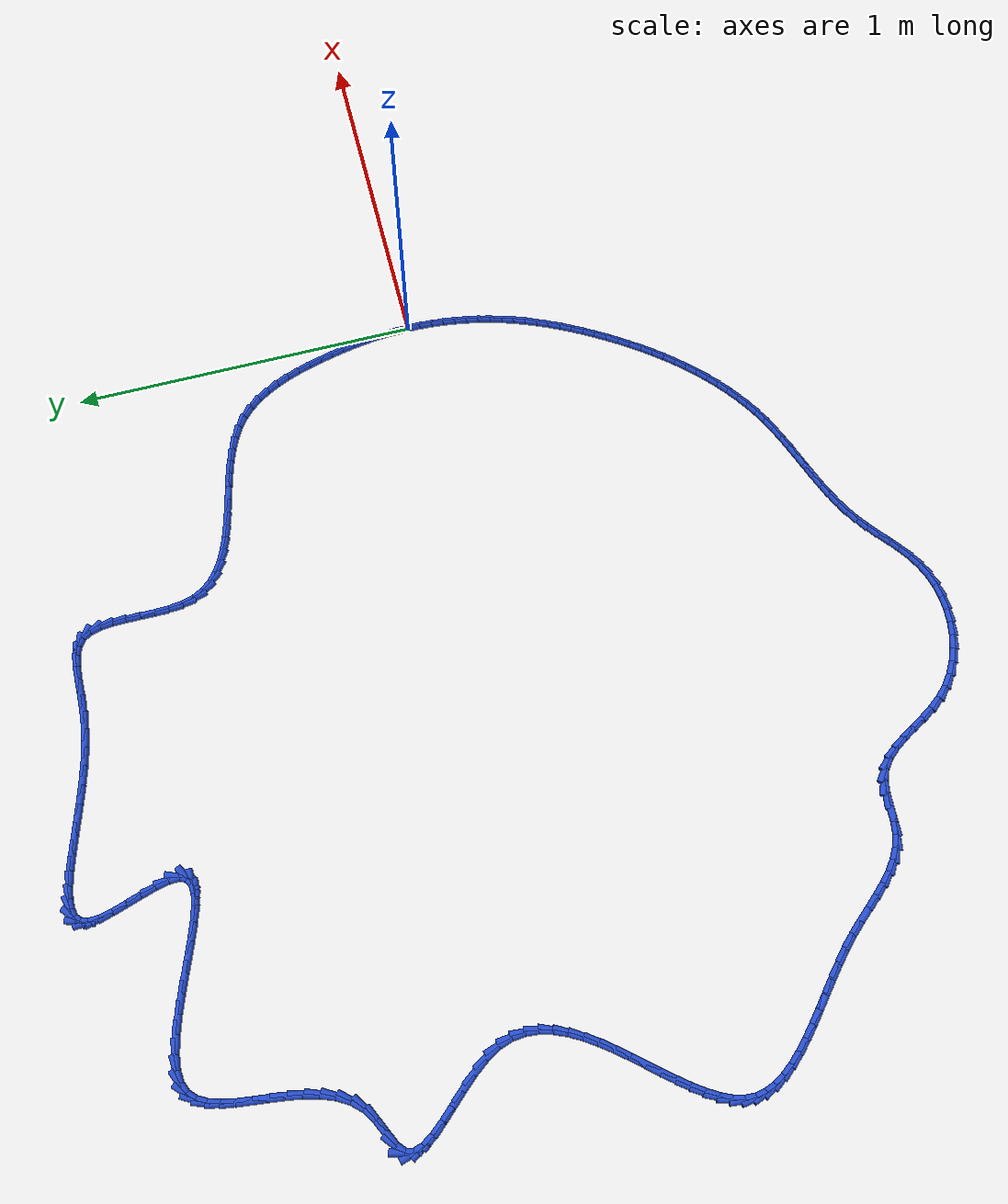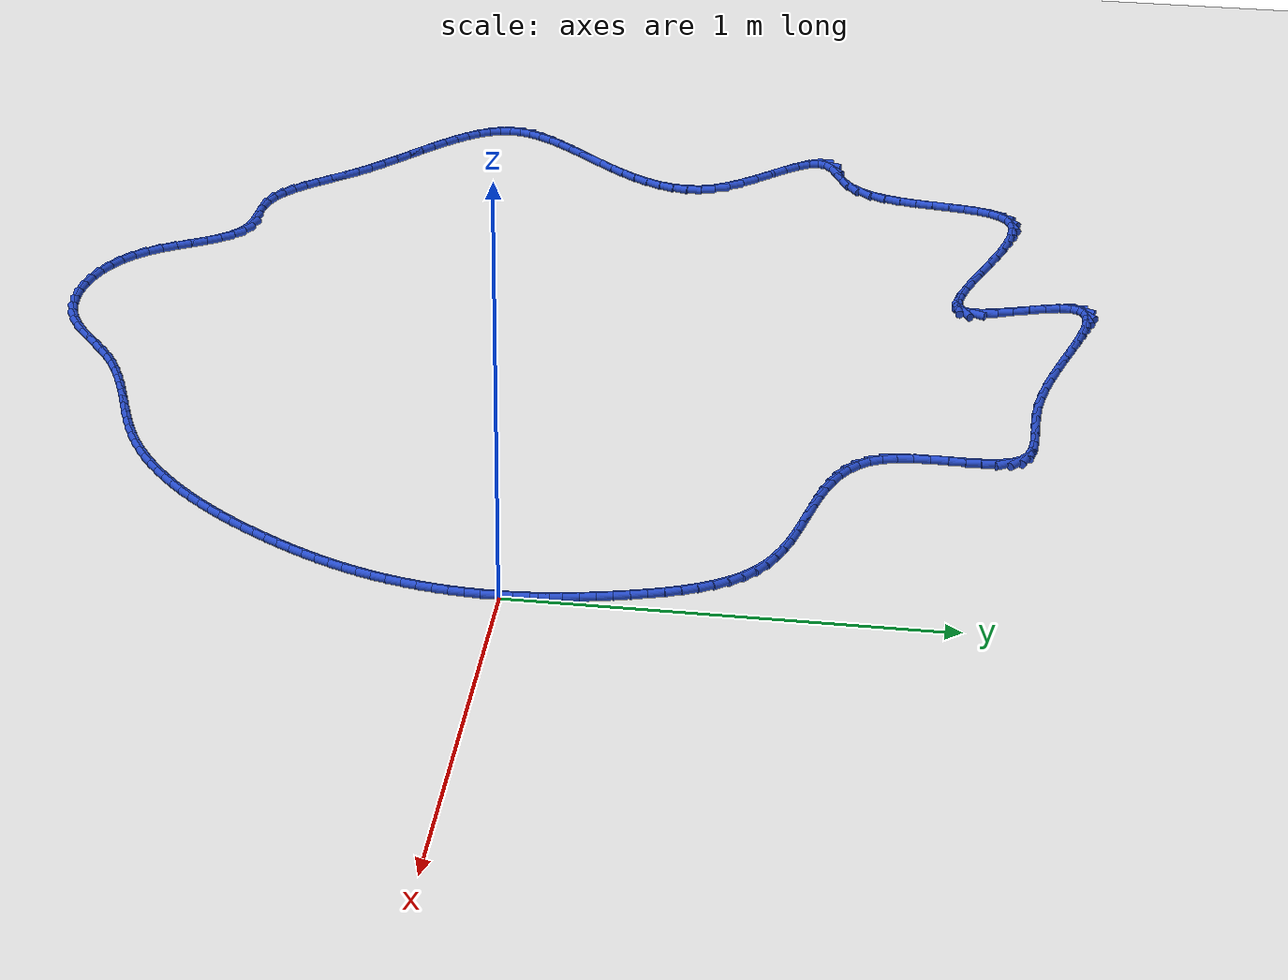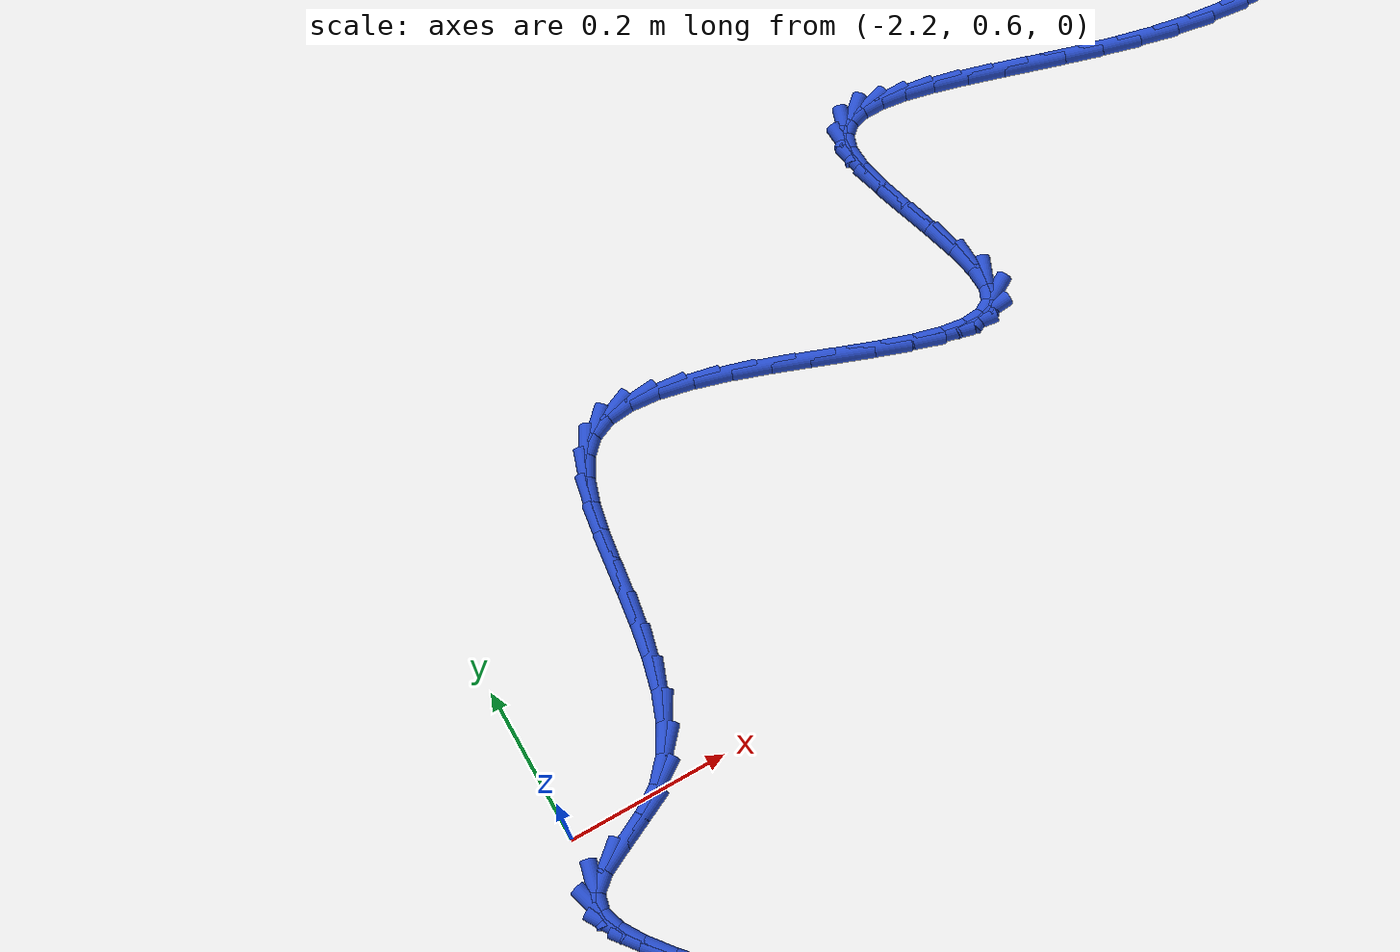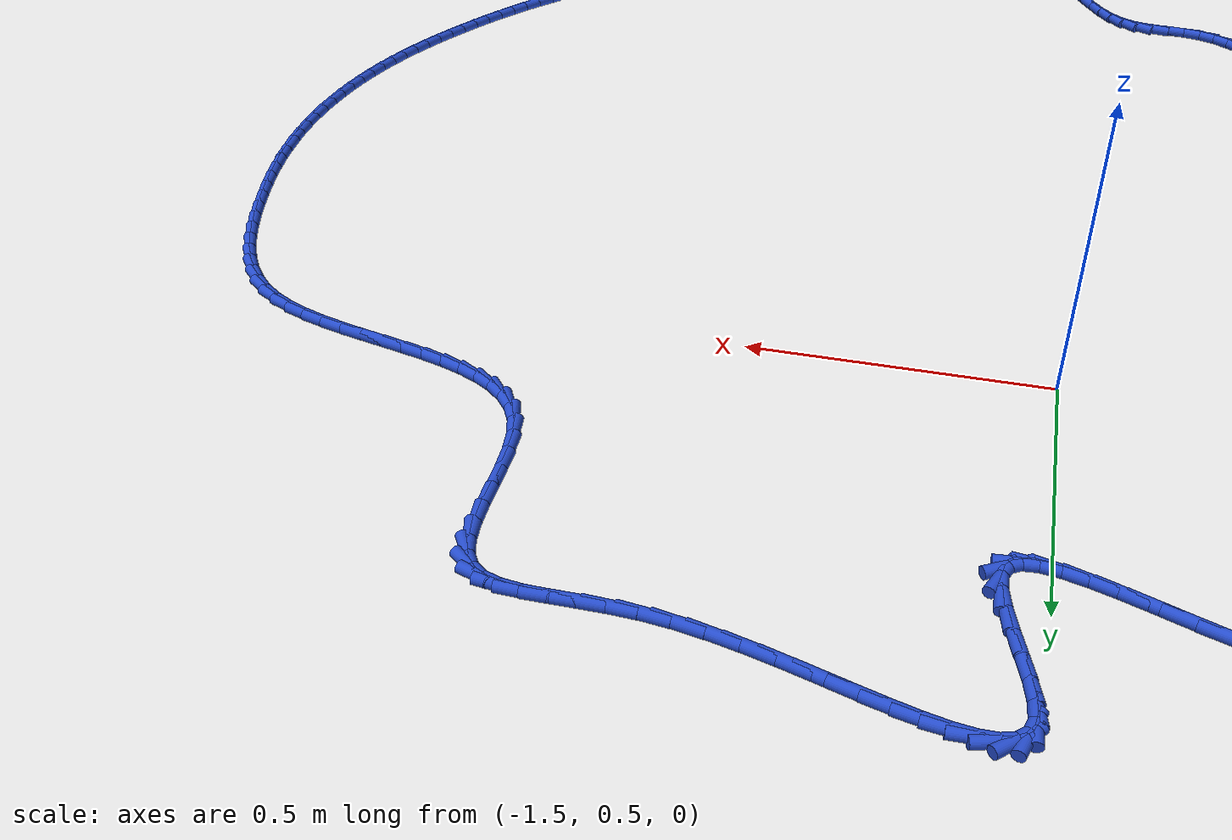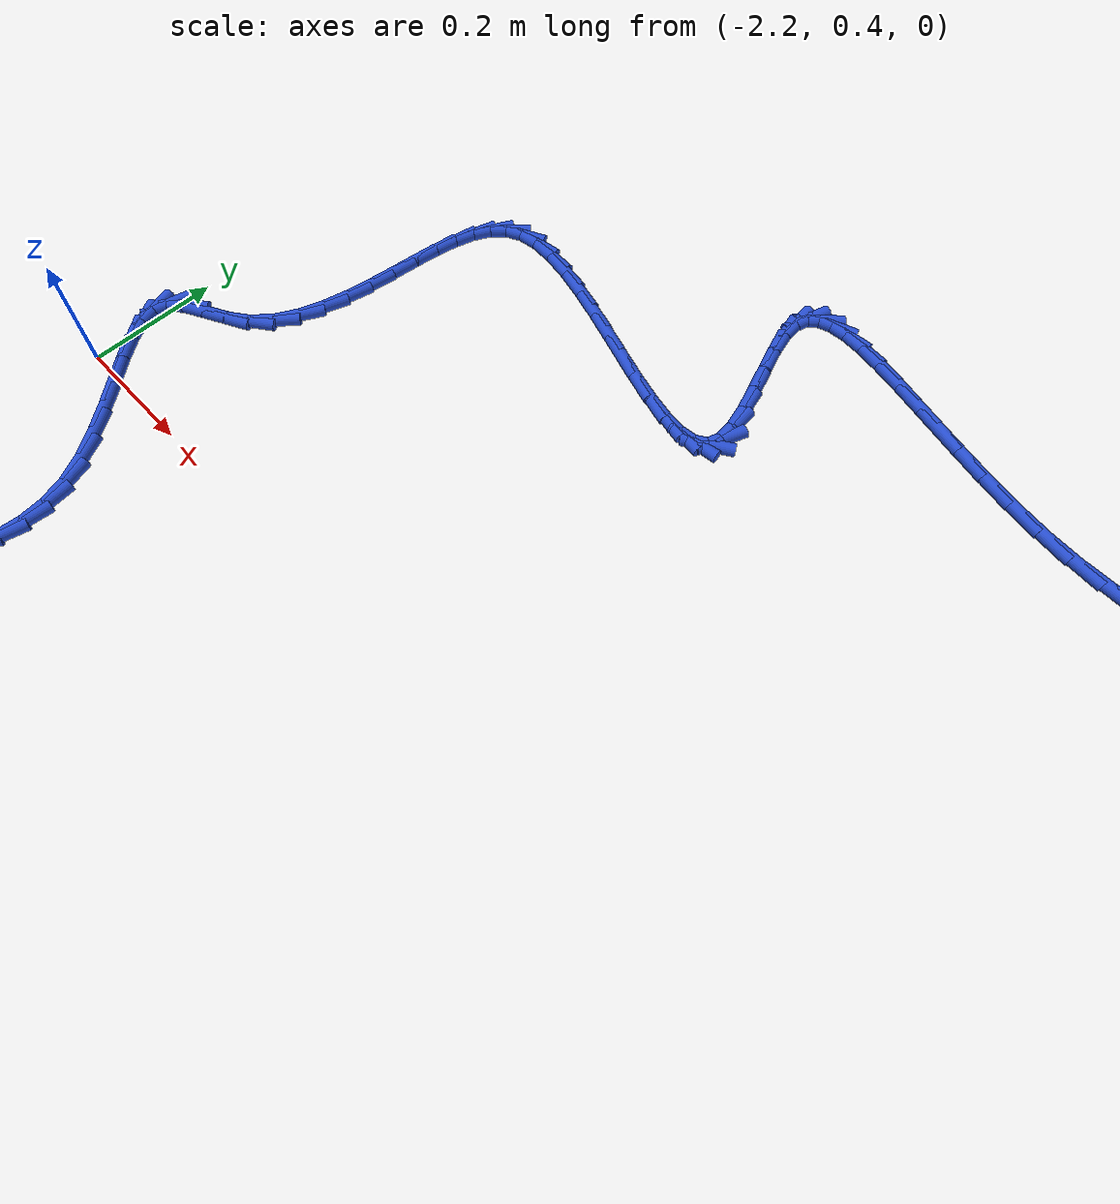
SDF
<sdf version="1.6">
 <world name="default">
  <light name="sun" type="directional">
   <pose>0 0 10 0 -0 0</pose>
   <diffuse>0.8 0.8 0.8 1</diffuse>
   <specular>0.2 0.2 0.2 1</specular>
   <attenuation>
    <range>1000</range>
    <constant>0.9</constant>
    <linear>0.01</linear>
    <quadratic>0.001</quadratic>
   </attenuation>
   <direction>-0.5 0.1 -0.9</direction>
  </light>
  <model name="ground_plane">
   <static>1</static>
   <link name="link">
    <collision name="collision">
     <geometry><plane><normal>0 0 1</normal><size>100 100</size></plane></geometry>
     <surface><friction><ode><mu>100</mu><mu2>50</mu2></ode></friction></surface>
    </collision>
    <visual name="visual">
     <cast_shadows>0</cast_shadows>
     <geometry><plane><normal>0 0 1</normal><size>100 100</size></plane></geometry>
     <material>
      <script><uri>file://media/materials/scripts/gazebo.material</uri><name>Gazebo/WhiteGlow</name></script>
     </material>
    </visual>
   </link>
  </model>
  <gravity>0 0 -9.8</gravity>
  <magnetic_field>6e-06 2.3e-05 -4.2e-05</magnetic_field>
  <atmosphere type="adiabatic"/>
  <physics name="default_physics" default="0" type="ode">
   <max_step_size>0.001</max_step_size>
   <real_time_factor>1</real_time_factor>
   <real_time_update_rate>1000</real_time_update_rate>
  </physics>
  <scene><ambient>0.4 0.4 0.4 1</ambient><background>0.7 0.7 0.7 1</background><shadows>1</shadows></scene>
  <spherical_coordinates>
   <surface_model>EARTH_WGS84</surface_model>
   <latitude_deg>0</latitude_deg>
   <longitude_deg>0</longitude_deg>
   <elevation>0</elevation>
   <heading_deg>0</heading_deg>
  </spherical_coordinates>
  <model name="line">
   <link name="link_0">
    <pose>-2.3418766925686896e-17 -5.551115123125783e-17 0.01 0 1.57 -1.5443511170814799</pose>
    <collision name="collision">
     <geometry><cylinder><radius>0.01</radius><length>0.08</length></cylinder></geometry>
    </collision>
    <visual name="visual">
     <material>
      <script><name>Gazebo/Blue</name><uri>file://media/materials/scripts/gazebo.material</uri></script>
     </material>
     <geometry><cylinder><radius>0.01</radius><length>0.08</length></cylinder></geometry>
    </visual>
   </link>
   <link name="link_1">
    <pose>-0.0009356074403868832 0.035370841636036085 0.01 0 1.57 -1.507399399484923</pose>
    <collision name="collision">
     <geometry><cylinder><radius>0.01</radius><length>0.08</length></cylinder></geometry>
    </collision>
    <visual name="visual">
     <material>
      <script><name>Gazebo/Blue</name><uri>file://media/materials/scripts/gazebo.material</uri></script>
     </material>
     <geometry><cylinder><radius>0.01</radius><length>0.08</length></cylinder></geometry>
    </visual>
   </link>
   <link name="link_2">
    <pose>-0.0031719264508817844 0.07059845049854166 0.01 0 1.57 -1.4721156726826294</pose>
    <collision name="collision">
     <geometry><cylinder><radius>0.01</radius><length>0.08</length></cylinder></geometry>
    </collision>
    <visual name="visual">
     <material>
      <script><name>Gazebo/Blue</name><uri>file://media/materials/scripts/gazebo.material</uri></script>
     </material>
     <geometry><cylinder><radius>0.01</radius><length>0.08</length></cylinder></geometry>
    </visual>
   </link>
   <link name="link_3">
    <pose>-0.006651490476367418 0.10574477377533564 0.01 0 1.57 -1.4387554516161924</pose>
    <collision name="collision">
     <geometry><cylinder><radius>0.01</radius><length>0.08</length></cylinder></geometry>
    </collision>
    <visual name="visual">
     <material>
      <script><name>Gazebo/Blue</name><uri>file://media/materials/scripts/gazebo.material</uri></script>
     </material>
     <geometry><cylinder><radius>0.01</radius><length>0.08</length></cylinder></geometry>
    </visual>
   </link>
   <link name="link_4">
    <pose>-0.01131683296172649 0.14087175865423707 0.01 0 1.57 -1.4075279342403777</pose>
    <collision name="collision">
     <geometry><cylinder><radius>0.01</radius><length>0.08</length></cylinder></geometry>
    </collision>
    <visual name="visual">
     <material>
      <script><name>Gazebo/Blue</name><uri>file://media/materials/scripts/gazebo.material</uri></script>
     </material>
     <geometry><cylinder><radius>0.01</radius><length>0.08</length></cylinder></geometry>
    </visual>
   </link>
   <link name="link_5">
    <pose>-0.017110487351841692 0.17604135232306473 0.01 0 1.57 -1.3785943222353751</pose>
    <collision name="collision">
     <geometry><cylinder><radius>0.01</radius><length>0.08</length></cylinder></geometry>
    </collision>
    <visual name="visual">
     <material>
      <script><name>Gazebo/Blue</name><uri>file://media/materials/scripts/gazebo.material</uri></script>
     </material>
     <geometry><cylinder><radius>0.01</radius><length>0.08</length></cylinder></geometry>
    </visual>
   </link>
   <link name="link_6">
    <pose>-0.023974987091595713 0.21131550196963764 0.01 0 1.57 -1.3520688212633551</pose>
    <collision name="collision">
     <geometry><cylinder><radius>0.01</radius><length>0.08</length></cylinder></geometry>
    </collision>
    <visual name="visual">
     <material>
      <script><name>Gazebo/Blue</name><uri>file://media/materials/scripts/gazebo.material</uri></script>
     </material>
     <geometry><cylinder><radius>0.01</radius><length>0.08</length></cylinder></geometry>
    </visual>
   </link>
   <link name="link_7">
    <pose>-0.031852865625871266 0.24675615478177482 0.01 0 1.57 -1.328021720045371</pose>
    <collision name="collision">
     <geometry><cylinder><radius>0.01</radius><length>0.08</length></cylinder></geometry>
    </collision>
    <visual name="visual">
     <material>
      <script><name>Gazebo/Blue</name><uri>file://media/materials/scripts/gazebo.material</uri></script>
     </material>
     <geometry><cylinder><radius>0.01</radius><length>0.08</length></cylinder></geometry>
    </visual>
   </link>
   <link name="link_8">
    <pose>-0.040686656863631175 0.2824252572989774 0.01 0 1.57 -1.3040560741518854</pose>
    <collision name="collision">
     <geometry><cylinder><radius>0.01</radius><length>0.08</length></cylinder></geometry>
    </collision>
    <visual name="visual">
     <material>
      <script><name>Gazebo/Blue</name><uri>file://media/materials/scripts/gazebo.material</uri></script>
     </material>
     <geometry><cylinder><radius>0.01</radius><length>0.08</length></cylinder></geometry>
    </visual>
   </link>
   <link name="link_9">
    <pose>-0.05048675306662822 0.3182899582650312 0.01 0 1.57 -1.2708214964377482</pose>
    <collision name="collision">
     <geometry><cylinder><radius>0.01</radius><length>0.08</length></cylinder></geometry>
    </collision>
    <visual name="visual">
     <material>
      <script><name>Gazebo/Blue</name><uri>file://media/materials/scripts/gazebo.material</uri></script>
     </material>
     <geometry><cylinder><radius>0.01</radius><length>0.08</length></cylinder></geometry>
    </visual>
   </link>
   <link name="link_10">
    <pose>-0.06151967945063391 0.35395958990662735 0.01 0 1.57 -1.225420641354258</pose>
    <collision name="collision">
     <geometry><cylinder><radius>0.01</radius><length>0.08</length></cylinder></geometry>
    </collision>
    <visual name="visual">
     <material>
      <script><name>Gazebo/Blue</name><uri>file://media/materials/scripts/gazebo.material</uri></script>
     </material>
     <geometry><cylinder><radius>0.01</radius><length>0.08</length></cylinder></geometry>
    </visual>
   </link>
   <link name="link_11">
    <pose>-0.07411238267048821 0.38895907598779705 0.01 0 1.57 -1.1666420314949255</pose>
    <collision name="collision">
     <geometry><cylinder><radius>0.01</radius><length>0.08</length></cylinder></geometry>
    </collision>
    <visual name="visual">
     <material>
      <script><name>Gazebo/Blue</name><uri>file://media/materials/scripts/gazebo.material</uri></script>
     </material>
     <geometry><cylinder><radius>0.01</radius><length>0.08</length></cylinder></geometry>
    </visual>
   </link>
   <link name="link_12">
    <pose>-0.08859180938103112 0.4228133402725714 0.01 0 1.57 -1.0929528645879047</pose>
    <collision name="collision">
     <geometry><cylinder><radius>0.01</radius><length>0.08</length></cylinder></geometry>
    </collision>
    <visual name="visual">
     <material>
      <script><name>Gazebo/Blue</name><uri>file://media/materials/scripts/gazebo.material</uri></script>
     </material>
     <geometry><cylinder><radius>0.01</radius><length>0.08</length></cylinder></geometry>
    </visual>
   </link>
   <link name="link_13">
    <pose>-0.1052849062371026 0.4550473065249816 0.01 0 1.57 -1.0027784844517484</pose>
    <collision name="collision">
     <geometry><cylinder><radius>0.01</radius><length>0.08</length></cylinder></geometry>
    </collision>
    <visual name="visual">
     <material>
      <script><name>Gazebo/Blue</name><uri>file://media/materials/scripts/gazebo.material</uri></script>
     </material>
     <geometry><cylinder><radius>0.01</radius><length>0.08</length></cylinder></geometry>
    </visual>
   </link>
   <link name="link_14">
    <pose>-0.1245186198935426 0.48518589850905874 0.01 0 1.57 -0.8950219088581098</pose>
    <collision name="collision">
     <geometry><cylinder><radius>0.01</radius><length>0.08</length></cylinder></geometry>
    </collision>
    <visual name="visual">
     <material>
      <script><name>Gazebo/Blue</name><uri>file://media/materials/scripts/gazebo.material</uri></script>
     </material>
     <geometry><cylinder><radius>0.01</radius><length>0.08</length></cylinder></geometry>
    </visual>
   </link>
   <link name="link_15">
    <pose>-0.1466198970051911 0.5127540399888337 0.01 0 1.57 -0.7698795922657101</pose>
    <collision name="collision">
     <geometry><cylinder><radius>0.01</radius><length>0.08</length></cylinder></geometry>
    </collision>
    <visual name="visual">
     <material>
      <script><name>Gazebo/Blue</name><uri>file://media/materials/scripts/gazebo.material</uri></script>
     </material>
     <geometry><cylinder><radius>0.01</radius><length>0.08</length></cylinder></geometry>
    </visual>
   </link>
   <link name="link_16">
    <pose>-0.1719156842268881 0.5372766547283382 0.01 0 1.57 -0.631048806607177</pose>
    <collision name="collision">
     <geometry><cylinder><radius>0.01</radius><length>0.08</length></cylinder></geometry>
    </collision>
    <visual name="visual">
     <material>
      <script><name>Gazebo/Blue</name><uri>file://media/materials/scripts/gazebo.material</uri></script>
     </material>
     <geometry><cylinder><radius>0.01</radius><length>0.08</length></cylinder></geometry>
    </visual>
   </link>
   <link name="link_17">
    <pose>-0.20070284013961703 0.558312072084475 0.01 0 1.57 -0.5029700494168633</pose>
    <collision name="collision">
     <geometry><cylinder><radius>0.01</radius><length>0.08</length></cylinder></geometry>
    </collision>
    <visual name="visual">
     <material>
      <script><name>Gazebo/Blue</name><uri>file://media/materials/scripts/gazebo.material</uri></script>
     </material>
     <geometry><cylinder><radius>0.01</radius><length>0.08</length></cylinder></geometry>
    </visual>
   </link>
   <link name="link_18">
    <pose>-0.23278720852678672 0.5759637756337271 0.01 0 1.57 -0.40262355745853357</pose>
    <collision name="collision">
     <geometry><cylinder><radius>0.01</radius><length>0.08</length></cylinder></geometry>
    </collision>
    <visual name="visual">
     <material>
      <script><name>Gazebo/Blue</name><uri>file://media/materials/scripts/gazebo.material</uri></script>
     </material>
     <geometry><cylinder><radius>0.01</radius><length>0.08</length></cylinder></geometry>
    </visual>
   </link>
   <link name="link_19">
    <pose>-0.267574626240588 0.5907793607542833 0.01 0 1.57 -0.3277192849105629</pose>
    <collision name="collision">
     <geometry><cylinder><radius>0.01</radius><length>0.08</length></cylinder></geometry>
    </collision>
    <visual name="visual">
     <material>
      <script><name>Gazebo/Blue</name><uri>file://media/materials/scripts/gazebo.material</uri></script>
     </material>
     <geometry><cylinder><radius>0.01</radius><length>0.08</length></cylinder></geometry>
    </visual>
   </link>
   <link name="link_20">
    <pose>-0.30445928373605347 0.6033193533563338 0.01 0 1.57 -0.27493159539339396</pose>
    <collision name="collision">
     <geometry><cylinder><radius>0.01</radius><length>0.08</length></cylinder></geometry>
    </collision>
    <visual name="visual">
     <material>
      <script><name>Gazebo/Blue</name><uri>file://media/materials/scripts/gazebo.material</uri></script>
     </material>
     <geometry><cylinder><radius>0.01</radius><length>0.08</length></cylinder></geometry>
    </visual>
   </link>
   <link name="link_21">
    <pose>-0.3428353714682156 0.6141442793500697 0.01 0 1.57 -0.2414987292422664</pose>
    <collision name="collision">
     <geometry><cylinder><radius>0.01</radius><length>0.08</length></cylinder></geometry>
    </collision>
    <visual name="visual">
     <material>
      <script><name>Gazebo/Blue</name><uri>file://media/materials/scripts/gazebo.material</uri></script>
     </material>
     <geometry><cylinder><radius>0.01</radius><length>0.08</length></cylinder></geometry>
    </visual>
   </link>
   <link name="link_22">
    <pose>-0.3820970798921073 0.6238146646456812 0.01 0 1.57 -0.22563169829701232</pose>
    <collision name="collision">
     <geometry><cylinder><radius>0.01</radius><length>0.08</length></cylinder></geometry>
    </collision>
    <visual name="visual">
     <material>
      <script><name>Gazebo/Blue</name><uri>file://media/materials/scripts/gazebo.material</uri></script>
     </material>
     <geometry><cylinder><radius>0.01</radius><length>0.08</length></cylinder></geometry>
    </visual>
   </link>
   <link name="link_23">
    <pose>-0.4216385994627611 0.6328910351533592 0.01 0 1.57 -0.22663290043007644</pose>
    <collision name="collision">
     <geometry><cylinder><radius>0.01</radius><length>0.08</length></cylinder></geometry>
    </collision>
    <visual name="visual">
     <material>
      <script><name>Gazebo/Blue</name><uri>file://media/materials/scripts/gazebo.material</uri></script>
     </material>
     <geometry><cylinder><radius>0.01</radius><length>0.08</length></cylinder></geometry>
    </visual>
   </link>
   <link name="link_24">
    <pose>-0.4608541206352096 0.6419339167832943 0.01 0 1.57 -0.24495384160686315</pose>
    <collision name="collision">
     <geometry><cylinder><radius>0.01</radius><length>0.08</length></cylinder></geometry>
    </collision>
    <visual name="visual">
     <material>
      <script><name>Gazebo/Blue</name><uri>file://media/materials/scripts/gazebo.material</uri></script>
     </material>
     <geometry><cylinder><radius>0.01</radius><length>0.08</length></cylinder></geometry>
    </visual>
   </link>
   <link name="link_25">
    <pose>-0.49913783386448574 0.6515038354456776 0.01 0 1.57 -0.28228538208518905</pose>
    <collision name="collision">
     <geometry><cylinder><radius>0.01</radius><length>0.08</length></cylinder></geometry>
    </collision>
    <visual name="visual">
     <material>
      <script><name>Gazebo/Blue</name><uri>file://media/materials/scripts/gazebo.material</uri></script>
     </material>
     <geometry><cylinder><radius>0.01</radius><length>0.08</length></cylinder></geometry>
    </visual>
   </link>
   <link name="link_26">
    <pose>-0.5358839296056216 0.662161317050699 0.01 0 1.57 -0.3416770474934047</pose>
    <collision name="collision">
     <geometry><cylinder><radius>0.01</radius><length>0.08</length></cylinder></geometry>
    </collision>
    <visual name="visual">
     <material>
      <script><name>Gazebo/Blue</name><uri>file://media/materials/scripts/gazebo.material</uri></script>
     </material>
     <geometry><cylinder><radius>0.01</radius><length>0.08</length></cylinder></geometry>
    </visual>
   </link>
   <link name="link_27">
    <pose>-0.5704865983136503 0.6744668875085497 0.01 0 1.57 -0.4275469131294563</pose>
    <collision name="collision">
     <geometry><cylinder><radius>0.01</radius><length>0.08</length></cylinder></geometry>
    </collision>
    <visual name="visual">
     <material>
      <script><name>Gazebo/Blue</name><uri>file://media/materials/scripts/gazebo.material</uri></script>
     </material>
     <geometry><cylinder><radius>0.01</radius><length>0.08</length></cylinder></geometry>
    </visual>
   </link>
   <link name="link_28">
    <pose>-0.6023400304436043 0.6889810727294201 0.01 0 1.57 -0.5451609611070342</pose>
    <collision name="collision">
     <geometry><cylinder><radius>0.01</radius><length>0.08</length></cylinder></geometry>
    </collision>
    <visual name="visual">
     <material>
      <script><name>Gazebo/Blue</name><uri>file://media/materials/scripts/gazebo.material</uri></script>
     </material>
     <geometry><cylinder><radius>0.01</radius><length>0.08</length></cylinder></geometry>
    </visual>
   </link>
   <link name="link_29">
    <pose>-0.6308384164505163 0.7062643986235011 0.01 0 1.57 -0.6986948762659486</pose>
    <collision name="collision">
     <geometry><cylinder><radius>0.01</radius><length>0.08</length></cylinder></geometry>
    </collision>
    <visual name="visual">
     <material>
      <script><name>Gazebo/Blue</name><uri>file://media/materials/scripts/gazebo.material</uri></script>
     </material>
     <geometry><cylinder><radius>0.01</radius><length>0.08</length></cylinder></geometry>
    </visual>
   </link>
   <link name="link_30">
    <pose>-0.655375946789419 0.7268773911009834 0.01 0 1.57 -0.8869568642156067</pose>
    <collision name="collision">
     <geometry><cylinder><radius>0.01</radius><length>0.08</length></cylinder></geometry>
    </collision>
    <visual name="visual">
     <material>
      <script><name>Gazebo/Blue</name><uri>file://media/materials/scripts/gazebo.material</uri></script>
     </material>
     <geometry><cylinder><radius>0.01</radius><length>0.08</length></cylinder></geometry>
    </visual>
   </link>
   <link name="link_31">
    <pose>-0.6753468119153448 0.7513805760720571 0.01 0 1.57 -1.0983068221468184</pose>
    <collision name="collision">
     <geometry><cylinder><radius>0.01</radius><length>0.08</length></cylinder></geometry>
    </collision>
    <visual name="visual">
     <material>
      <script><name>Gazebo/Blue</name><uri>file://media/materials/scripts/gazebo.material</uri></script>
     </material>
     <geometry><cylinder><radius>0.01</radius><length>0.08</length></cylinder></geometry>
    </visual>
   </link>
   <link name="link_32">
    <pose>-0.6901452022833267 0.7803344794469136 0.01 0 1.57 -1.304767397000657</pose>
    <collision name="collision">
     <geometry><cylinder><radius>0.01</radius><length>0.08</length></cylinder></geometry>
    </collision>
    <visual name="visual">
     <material>
      <script><name>Gazebo/Blue</name><uri>file://media/materials/scripts/gazebo.material</uri></script>
     </material>
     <geometry><cylinder><radius>0.01</radius><length>0.08</length></cylinder></geometry>
    </visual>
   </link>
   <link name="link_33">
    <pose>-0.6993503481458103 0.8141163719011468 0.01 0 1.57 -1.4513886290767635</pose>
    <collision name="collision">
     <geometry><cylinder><radius>0.01</radius><length>0.08</length></cylinder></geometry>
    </collision>
    <visual name="visual">
     <material>
      <script><name>Gazebo/Blue</name><uri>file://media/materials/scripts/gazebo.material</uri></script>
     </material>
     <geometry><cylinder><radius>0.01</radius><length>0.08</length></cylinder></geometry>
    </visual>
   </link>
   <link name="link_34">
    <pose>-0.7038700985597063 0.8517877187857396 0.01 0 1.57 -1.5377775892442451</pose>
    <collision name="collision">
     <geometry><cylinder><radius>0.01</radius><length>0.08</length></cylinder></geometry>
    </collision>
    <visual name="visual">
     <material>
      <script><name>Gazebo/Blue</name><uri>file://media/materials/scripts/gazebo.material</uri></script>
     </material>
     <geometry><cylinder><radius>0.01</radius><length>0.08</length></cylinder></geometry>
    </visual>
   </link>
   <link name="link_35">
    <pose>-0.7051928898969547 0.8918349974431133 0.01 0 1.57 1.5614266939043104</pose>
    <collision name="collision">
     <geometry><cylinder><radius>0.01</radius><length>0.08</length></cylinder></geometry>
    </collision>
    <visual name="visual">
     <material>
      <script><name>Gazebo/Blue</name><uri>file://media/materials/scripts/gazebo.material</uri></script>
     </material>
     <geometry><cylinder><radius>0.01</radius><length>0.08</length></cylinder></geometry>
    </visual>
   </link>
   <link name="link_36">
    <pose>-0.7048095925097905 0.932742274709213 0.01 0 1.57 1.5559279618136346</pose>
    <collision name="collision">
     <geometry><cylinder><radius>0.01</radius><length>0.08</length></cylinder></geometry>
    </collision>
    <visual name="visual">
     <material>
      <script><name>Gazebo/Blue</name><uri>file://media/materials/scripts/gazebo.material</uri></script>
     </material>
     <geometry><cylinder><radius>0.01</radius><length>0.08</length></cylinder></geometry>
    </visual>
   </link>
   <link name="link_37">
    <pose>-0.7042110767504483 0.9729936174199837 0.01 0 1.57 -1.5530160169854506</pose>
    <collision name="collision">
     <geometry><cylinder><radius>0.01</radius><length>0.08</length></cylinder></geometry>
    </collision>
    <visual name="visual">
     <material>
      <script><name>Gazebo/Blue</name><uri>file://media/materials/scripts/gazebo.material</uri></script>
     </material>
     <geometry><cylinder><radius>0.01</radius><length>0.08</length></cylinder></geometry>
    </visual>
   </link>
   <link name="link_38">
    <pose>-0.7048882129711634 1.0110730924113704 0.01 0 1.57 -1.4709983808611913</pose>
    <collision name="collision">
     <geometry><cylinder><radius>0.01</radius><length>0.08</length></cylinder></geometry>
    </collision>
    <visual name="visual">
     <material>
      <script><name>Gazebo/Blue</name><uri>file://media/materials/scripts/gazebo.material</uri></script>
     </material>
     <geometry><cylinder><radius>0.01</radius><length>0.08</length></cylinder></geometry>
    </visual>
   </link>
   <link name="link_39">
    <pose>-0.7083318715241704 1.0454647665193184 0.01 0 1.57 -1.3128314240442829</pose>
    <collision name="collision">
     <geometry><cylinder><radius>0.01</radius><length>0.08</length></cylinder></geometry>
    </collision>
    <visual name="visual">
     <material>
      <script><name>Gazebo/Blue</name><uri>file://media/materials/scripts/gazebo.material</uri></script>
     </material>
     <geometry><cylinder><radius>0.01</radius><length>0.08</length></cylinder></geometry>
    </visual>
   </link>
   <link name="link_40">
    <pose>-0.7160329227617046 1.0746527065797729 0.01 0 1.57 -1.0314268278902456</pose>
    <collision name="collision">
     <geometry><cylinder><radius>0.01</radius><length>0.08</length></cylinder></geometry>
    </collision>
    <visual name="visual">
     <material>
      <script><name>Gazebo/Blue</name><uri>file://media/materials/scripts/gazebo.material</uri></script>
     </material>
     <geometry><cylinder><radius>0.01</radius><length>0.08</length></cylinder></geometry>
    </visual>
   </link>
   <link name="link_41">
    <pose>-0.7294820120841008 1.097121297116823 0.01 0 1.57 -0.6356567790762537</pose>
    <collision name="collision">
     <geometry><cylinder><radius>0.01</radius><length>0.08</length></cylinder></geometry>
    </collision>
    <visual name="visual">
     <material>
      <script><name>Gazebo/Blue</name><uri>file://media/materials/scripts/gazebo.material</uri></script>
     </material>
     <geometry><cylinder><radius>0.01</radius><length>0.08</length></cylinder></geometry>
    </visual>
   </link>
   <link name="link_42">
    <pose>-0.7496906750294795 1.112031545183198 0.01 0 1.57 -0.3145713084228156</pose>
    <collision name="collision">
     <geometry><cylinder><radius>0.01</radius><length>0.08</length></cylinder></geometry>
    </collision>
    <visual name="visual">
     <material>
      <script><name>Gazebo/Blue</name><uri>file://media/materials/scripts/gazebo.material</uri></script>
     </material>
     <geometry><cylinder><radius>0.01</radius><length>0.08</length></cylinder></geometry>
    </visual>
   </link>
   <link name="link_43">
    <pose>-0.7761793228513663 1.1206502969376975 0.01 0 1.57 -0.12443586693087837</pose>
    <collision name="collision">
     <geometry><cylinder><radius>0.01</radius><length>0.08</length></cylinder></geometry>
    </collision>
    <visual name="visual">
     <material>
      <script><name>Gazebo/Blue</name><uri>file://media/materials/scripts/gazebo.material</uri></script>
     </material>
     <geometry><cylinder><radius>0.01</radius><length>0.08</length></cylinder></geometry>
    </visual>
   </link>
   <link name="link_44">
    <pose>-0.8081791116526986 1.1246528988995768 0.01 0 1.57 -0.028890663913331574</pose>
    <collision name="collision">
     <geometry><cylinder><radius>0.01</radius><length>0.08</length></cylinder></geometry>
    </collision>
    <visual name="visual">
     <material>
      <script><name>Gazebo/Blue</name><uri>file://media/materials/scripts/gazebo.material</uri></script>
     </material>
     <geometry><cylinder><radius>0.01</radius><length>0.08</length></cylinder></geometry>
    </visual>
   </link>
   <link name="link_45">
    <pose>-0.844921197536414 1.1257146975880914 0.01 0 1.57 0.005001932229973916</pose>
    <collision name="collision">
     <geometry><cylinder><radius>0.01</radius><length>0.08</length></cylinder></geometry>
    </collision>
    <visual name="visual">
     <material>
      <script><name>Gazebo/Blue</name><uri>file://media/materials/scripts/gazebo.material</uri></script>
     </material>
     <geometry><cylinder><radius>0.01</radius><length>0.08</length></cylinder></geometry>
    </visual>
   </link>
   <link name="link_46">
    <pose>-0.8856367366054508 1.1255110395224959 0.01 0 1.57 -0.004695571202951977</pose>
    <collision name="collision">
     <geometry><cylinder><radius>0.01</radius><length>0.08</length></cylinder></geometry>
    </collision>
    <visual name="visual">
     <material>
      <script><name>Gazebo/Blue</name><uri>file://media/materials/scripts/gazebo.material</uri></script>
     </material>
     <geometry><cylinder><radius>0.01</radius><length>0.08</length></cylinder></geometry>
    </visual>
   </link>
   <link name="link_47">
    <pose>-0.9295568849627464 1.1257172712220462 0.01 0 1.57 -0.049391849032370545</pose>
    <collision name="collision">
     <geometry><cylinder><radius>0.01</radius><length>0.08</length></cylinder></geometry>
    </collision>
    <visual name="visual">
     <material>
      <script><name>Gazebo/Blue</name><uri>file://media/materials/scripts/gazebo.material</uri></script>
     </material>
     <geometry><cylinder><radius>0.01</radius><length>0.08</length></cylinder></geometry>
    </visual>
   </link>
   <link name="link_48">
    <pose>-0.9759127987112381 1.1280087392059976 0.01 0 1.57 -0.12126209495058496</pose>
    <collision name="collision">
     <geometry><cylinder><radius>0.01</radius><length>0.08</length></cylinder></geometry>
    </collision>
    <visual name="visual">
     <material>
      <script><name>Gazebo/Blue</name><uri>file://media/materials/scripts/gazebo.material</uri></script>
     </material>
     <geometry><cylinder><radius>0.01</radius><length>0.08</length></cylinder></geometry>
    </visual>
   </link>
   <link name="link_49">
    <pose>-1.023941636699651 1.1338615323373513 0.01 0 1.57 -0.18732919693956782</pose>
    <collision name="collision">
     <geometry><cylinder><radius>0.01</radius><length>0.08</length></cylinder></geometry>
    </collision>
    <visual name="visual">
     <material>
      <script><name>Gazebo/Blue</name><uri>file://media/materials/scripts/gazebo.material</uri></script>
     </material>
     <geometry><cylinder><radius>0.01</radius><length>0.08</length></cylinder></geometry>
    </visual>
   </link>
   <link name="link_50">
    <pose>-1.0729288969393787 1.143147149079656 0.01 0 1.57 -0.2354410953516581</pose>
    <collision name="collision">
     <geometry><cylinder><radius>0.01</radius><length>0.08</length></cylinder></geometry>
    </collision>
    <visual name="visual">
     <material>
      <script><name>Gazebo/Blue</name><uri>file://media/materials/scripts/gazebo.material</uri></script>
     </material>
     <geometry><cylinder><radius>0.01</radius><length>0.08</length></cylinder></geometry>
    </visual>
   </link>
   <link name="link_51">
    <pose>-1.1221834027139739 1.1549628190489651 0.01 0 1.57 -0.26854711815059085</pose>
    <collision name="collision">
     <geometry><cylinder><radius>0.01</radius><length>0.08</length></cylinder></geometry>
    </collision>
    <visual name="visual">
     <material>
      <script><name>Gazebo/Blue</name><uri>file://media/materials/scripts/gazebo.material</uri></script>
     </material>
     <geometry><cylinder><radius>0.01</radius><length>0.08</length></cylinder></geometry>
    </visual>
   </link>
   <link name="link_52">
    <pose>-1.171014127964998 1.1684007708563413 0.01 0 1.57 -0.28833309087477643</pose>
    <collision name="collision">
     <geometry><cylinder><radius>0.01</radius><length>0.08</length></cylinder></geometry>
    </collision>
    <visual name="visual">
     <material>
      <script><name>Gazebo/Blue</name><uri>file://media/materials/scripts/gazebo.material</uri></script>
     </material>
     <geometry><cylinder><radius>0.01</radius><length>0.08</length></cylinder></geometry>
    </visual>
   </link>
   <link name="link_53">
    <pose>-1.2187300466340123 1.1825532331128457 0.01 0 1.57 -0.29517301512145183</pose>
    <collision name="collision">
     <geometry><cylinder><radius>0.01</radius><length>0.08</length></cylinder></geometry>
    </collision>
    <visual name="visual">
     <material>
      <script><name>Gazebo/Blue</name><uri>file://media/materials/scripts/gazebo.material</uri></script>
     </material>
     <geometry><cylinder><radius>0.01</radius><length>0.08</length></cylinder></geometry>
    </visual>
   </link>
   <link name="link_54">
    <pose>-1.2646401326625778 1.1965124344295408 0.01 0 1.57 -0.2879493658140747</pose>
    <collision name="collision">
     <geometry><cylinder><radius>0.01</radius><length>0.08</length></cylinder></geometry>
    </collision>
    <visual name="visual">
     <material>
      <script><name>Gazebo/Blue</name><uri>file://media/materials/scripts/gazebo.material</uri></script>
     </material>
     <geometry><cylinder><radius>0.01</radius><length>0.08</length></cylinder></geometry>
    </visual>
   </link>
   <link name="link_55">
    <pose>-1.3080533599922552 1.2093706034174876 0.01 0 1.57 -0.2634458789194492</pose>
    <collision name="collision">
     <geometry><cylinder><radius>0.01</radius><length>0.08</length></cylinder></geometry>
    </collision>
    <visual name="visual">
     <material>
      <script><name>Gazebo/Blue</name><uri>file://media/materials/scripts/gazebo.material</uri></script>
     </material>
     <geometry><cylinder><radius>0.01</radius><length>0.08</length></cylinder></geometry>
    </visual>
   </link>
   <link name="link_56">
    <pose>-1.3482787025646068 1.220219968687749 0.01 0 1.57 -0.214885247895679</pose>
    <collision name="collision">
     <geometry><cylinder><radius>0.01</radius><length>0.08</length></cylinder></geometry>
    </collision>
    <visual name="visual">
     <material>
      <script><name>Gazebo/Blue</name><uri>file://media/materials/scripts/gazebo.material</uri></script>
     </material>
     <geometry><cylinder><radius>0.01</radius><length>0.08</length></cylinder></geometry>
    </visual>
   </link>
   <link name="link_57">
    <pose>-1.384625134321193 1.2281527588513863 0.01 0 1.57 -0.1285786174697683</pose>
    <collision name="collision">
     <geometry><cylinder><radius>0.01</radius><length>0.08</length></cylinder></geometry>
    </collision>
    <visual name="visual">
     <material>
      <script><name>Gazebo/Blue</name><uri>file://media/materials/scripts/gazebo.material</uri></script>
     </material>
     <geometry><cylinder><radius>0.01</radius><length>0.08</length></cylinder></geometry>
    </visual>
   </link>
   <link name="link_58">
    <pose>-1.4164016292035744 1.232261202519461 0.01 0 1.57 0.023516753938039918</pose>
    <collision name="collision">
     <geometry><cylinder><radius>0.01</radius><length>0.08</length></cylinder></geometry>
    </collision>
    <visual name="visual">
     <material>
      <script><name>Gazebo/Blue</name><uri>file://media/materials/scripts/gazebo.material</uri></script>
     </material>
     <geometry><cylinder><radius>0.01</radius><length>0.08</length></cylinder></geometry>
    </visual>
   </link>
   <link name="link_59">
    <pose>-1.4429171611533131 1.2316375283030356 0.01 0 1.57 0.2956675362459462</pose>
    <collision name="collision">
     <geometry><cylinder><radius>0.01</radius><length>0.08</length></cylinder></geometry>
    </collision>
    <visual name="visual">
     <material>
      <script><name>Gazebo/Blue</name><uri>file://media/materials/scripts/gazebo.material</uri></script>
     </material>
     <geometry><cylinder><radius>0.01</radius><length>0.08</length></cylinder></geometry>
    </visual>
   </link>
   <link name="link_60">
    <pose>-1.46348070411197 1.2253739648131716 0.01 0 1.57 0.7439243515767405</pose>
    <collision name="collision">
     <geometry><cylinder><radius>0.01</radius><length>0.08</length></cylinder></geometry>
    </collision>
    <visual name="visual">
     <material>
      <script><name>Gazebo/Blue</name><uri>file://media/materials/scripts/gazebo.material</uri></script>
     </material>
     <geometry><cylinder><radius>0.01</radius><length>0.08</length></cylinder></geometry>
    </visual>
   </link>
   <link name="link_61">
    <pose>-1.477401232021106 1.212562740660931 0.01 0 1.57 1.25657230305741</pose>
    <collision name="collision">
     <geometry><cylinder><radius>0.01</radius><length>0.08</length></cylinder></geometry>
    </collision>
    <visual name="visual">
     <material>
      <script><name>Gazebo/Blue</name><uri>file://media/materials/scripts/gazebo.material</uri></script>
     </material>
     <geometry><cylinder><radius>0.01</radius><length>0.08</length></cylinder></geometry>
    </visual>
   </link>
   <link name="link_62">
    <pose>-1.4839877188222823 1.1922960844573756 0.01 0 1.57 -1.5275428245213711</pose>
    <collision name="collision">
     <geometry><cylinder><radius>0.01</radius><length>0.08</length></cylinder></geometry>
    </collision>
    <visual name="visual">
     <material>
      <script><name>Gazebo/Blue</name><uri>file://media/materials/scripts/gazebo.material</uri></script>
     </material>
     <geometry><cylinder><radius>0.01</radius><length>0.08</length></cylinder></geometry>
    </visual>
   </link>
   <link name="link_63">
    <pose>-1.4827585938555519 1.1638970347296829 0.01 0 1.57 -1.3582465226467408</pose>
    <collision name="collision">
     <geometry><cylinder><radius>0.01</radius><length>0.08</length></cylinder></geometry>
    </collision>
    <visual name="visual">
     <material>
      <script><name>Gazebo/Blue</name><uri>file://media/materials/scripts/gazebo.material</uri></script>
     </material>
     <geometry><cylinder><radius>0.01</radius><length>0.08</length></cylinder></geometry>
    </visual>
   </link>
   <link name="link_64">
    <pose>-1.4751955533008918 1.1288520569584548 0.01 0 1.57 -1.2879365823768223</pose>
    <collision name="collision">
     <geometry><cylinder><radius>0.01</radius><length>0.08</length></cylinder></geometry>
    </collision>
    <visual name="visual">
     <material>
      <script><name>Gazebo/Blue</name><uri>file://media/materials/scripts/gazebo.material</uri></script>
     </material>
     <geometry><cylinder><radius>0.01</radius><length>0.08</length></cylinder></geometry>
    </visual>
   </link>
   <link name="link_65">
    <pose>-1.463853855143631 1.089830630822174 0.01 0 1.57 -1.268921595184706</pose>
    <collision name="collision">
     <geometry><cylinder><radius>0.01</radius><length>0.08</length></cylinder></geometry>
    </collision>
    <visual name="visual">
     <material>
      <script><name>Gazebo/Blue</name><uri>file://media/materials/scripts/gazebo.material</uri></script>
     </material>
     <geometry><cylinder><radius>0.01</radius><length>0.08</length></cylinder></geometry>
    </visual>
   </link>
   <link name="link_66">
    <pose>-1.4512996816436092 1.0495142740317704 0.01 0 1.57 -1.290652962087507</pose>
    <collision name="collision">
     <geometry><cylinder><radius>0.01</radius><length>0.08</length></cylinder></geometry>
    </collision>
    <visual name="visual">
     <material>
      <script><name>Gazebo/Blue</name><uri>file://media/materials/scripts/gazebo.material</uri></script>
     </material>
     <geometry><cylinder><radius>0.01</radius><length>0.08</length></cylinder></geometry>
    </visual>
   </link>
   <link name="link_67">
    <pose>-1.4400992150606642 1.0105845042981756 0.01 0 1.57 -1.364913546421629</pose>
    <collision name="collision">
     <geometry><cylinder><radius>0.01</radius><length>0.08</length></cylinder></geometry>
    </collision>
    <visual name="visual">
     <material>
      <script><name>Gazebo/Blue</name><uri>file://media/materials/scripts/gazebo.material</uri></script>
     </material>
     <geometry><cylinder><radius>0.01</radius><length>0.08</length></cylinder></geometry>
    </visual>
   </link>
   <link name="link_68">
    <pose>-1.4328186376546355 0.9757228393323184 0.01 0 1.57 -1.5425417261412266</pose>
    <collision name="collision">
     <geometry><cylinder><radius>0.01</radius><length>0.08</length></cylinder></geometry>
    </collision>
    <visual name="visual">
     <material>
      <script><name>Gazebo/Blue</name><uri>file://media/materials/scripts/gazebo.material</uri></script>
     </material>
     <geometry><cylinder><radius>0.01</radius><length>0.08</length></cylinder></geometry>
    </visual>
   </link>
   <link name="link_69">
    <pose>-1.4320241316853617 0.9476107968451305 0.01 0 1.57 1.172215041694238</pose>
    <collision name="collision">
     <geometry><cylinder><radius>0.01</radius><length>0.08</length></cylinder></geometry>
    </collision>
    <visual name="visual">
     <material>
      <script><name>Gazebo/Blue</name><uri>file://media/materials/scripts/gazebo.material</uri></script>
     </material>
     <geometry><cylinder><radius>0.01</radius><length>0.08</length></cylinder></geometry>
    </visual>
   </link>
   <link name="link_70">
    <pose>-1.4400125933685064 0.9286413212481096 0.01 0 1.57 0.5327663946959821</pose>
    <collision name="collision">
     <geometry><cylinder><radius>0.01</radius><length>0.08</length></cylinder></geometry>
    </collision>
    <visual name="visual">
     <material>
      <script><name>Gazebo/Blue</name><uri>file://media/materials/scripts/gazebo.material</uri></script>
     </material>
     <geometry><cylinder><radius>0.01</radius><length>0.08</length></cylinder></geometry>
    </visual>
   </link>
   <link name="link_71">
    <pose>-1.4567878037543889 0.918750000459337 0.01 0 1.57 0.08665400599394021</pose>
    <collision name="collision">
     <geometry><cylinder><radius>0.01</radius><length>0.08</length></cylinder></geometry>
    </collision>
    <visual name="visual">
     <material>
      <script><name>Gazebo/Blue</name><uri>file://media/materials/scripts/gazebo.material</uri></script>
     </material>
     <geometry><cylinder><radius>0.01</radius><length>0.08</length></cylinder></geometry>
    </visual>
   </link>
   <link name="link_72">
    <pose>-1.4811939728964756 0.9166297986674977 0.01 0 1.57 -0.13948151157193725</pose>
    <collision name="collision">
     <geometry><cylinder><radius>0.01</radius><length>0.08</length></cylinder></geometry>
    </collision>
    <visual name="visual">
     <material>
      <script><name>Gazebo/Blue</name><uri>file://media/materials/scripts/gazebo.material</uri></script>
     </material>
     <geometry><cylinder><radius>0.01</radius><length>0.08</length></cylinder></geometry>
    </visual>
   </link>
   <link name="link_73">
    <pose>-1.5120663408580208 0.9209640676074299 0.01 0 1.57 -0.25609961996633385</pose>
    <collision name="collision">
     <geometry><cylinder><radius>0.01</radius><length>0.08</length></cylinder></geometry>
    </collision>
    <visual name="visual">
     <material>
      <script><name>Gazebo/Blue</name><uri>file://media/materials/scripts/gazebo.material</uri></script>
     </material>
     <geometry><cylinder><radius>0.01</radius><length>0.08</length></cylinder></geometry>
    </visual>
   </link>
   <link name="link_74">
    <pose>-1.54824014770228 0.9304361590139714 0.01 0 1.57 -0.3185418497809267</pose>
    <collision name="collision">
     <geometry><cylinder><radius>0.01</radius><length>0.08</length></cylinder></geometry>
    </collision>
    <visual name="visual">
     <material>
      <script><name>Gazebo/Blue</name><uri>file://media/materials/scripts/gazebo.material</uri></script>
     </material>
     <geometry><cylinder><radius>0.01</radius><length>0.08</length></cylinder></geometry>
    </visual>
   </link>
   <link name="link_75">
    <pose>-1.5885506334925077 0.9437294246219607 0.01 0 1.57 -0.3499690201473072</pose>
    <collision name="collision">
     <geometry><cylinder><radius>0.01</radius><length>0.08</length></cylinder></geometry>
    </collision>
    <visual name="visual">
     <material>
      <script><name>Gazebo/Blue</name><uri>file://media/materials/scripts/gazebo.material</uri></script>
     </material>
     <geometry><cylinder><radius>0.01</radius><length>0.08</length></cylinder></geometry>
    </visual>
   </link>
   <link name="link_76">
    <pose>-1.6318330382919588 0.9595272161662364 0.01 0 1.57 -0.3602686088512366</pose>
    <collision name="collision">
     <geometry><cylinder><radius>0.01</radius><length>0.08</length></cylinder></geometry>
    </collision>
    <visual name="visual">
     <material>
      <script><name>Gazebo/Blue</name><uri>file://media/materials/scripts/gazebo.material</uri></script>
     </material>
     <geometry><cylinder><radius>0.01</radius><length>0.08</length></cylinder></geometry>
    </visual>
   </link>
   <link name="link_77">
    <pose>-1.6769226021638879 0.9765128853816357 0.01 0 1.57 -0.3531498080925451</pose>
    <collision name="collision">
     <geometry><cylinder><radius>0.01</radius><length>0.08</length></cylinder></geometry>
    </collision>
    <visual name="visual">
     <material>
      <script><name>Gazebo/Blue</name><uri>file://media/materials/scripts/gazebo.material</uri></script>
     </material>
     <geometry><cylinder><radius>0.01</radius><length>0.08</length></cylinder></geometry>
    </visual>
   </link>
   <link name="link_78">
    <pose>-1.7226545651715508 0.9933697840029982 0.01 0 1.57 -0.328535640530899</pose>
    <collision name="collision">
     <geometry><cylinder><radius>0.01</radius><length>0.08</length></cylinder></geometry>
    </collision>
    <visual name="visual">
     <material>
      <script><name>Gazebo/Blue</name><uri>file://media/materials/scripts/gazebo.material</uri></script>
     </material>
     <geometry><cylinder><radius>0.01</radius><length>0.08</length></cylinder></geometry>
    </visual>
   </link>
   <link name="link_79">
    <pose>-1.7678641673782005 1.0087812637651603 0.01 0 1.57 -0.28284849062185324</pose>
    <collision name="collision">
     <geometry><cylinder><radius>0.01</radius><length>0.08</length></cylinder></geometry>
    </collision>
    <visual name="visual">
     <material>
      <script><name>Gazebo/Blue</name><uri>file://media/materials/scripts/gazebo.material</uri></script>
     </material>
     <geometry><cylinder><radius>0.01</radius><length>0.08</length></cylinder></geometry>
    </visual>
   </link>
   <link name="link_80">
    <pose>-1.811386648847094 1.0214306764029621 0.01 0 1.57 -0.20769553215215708</pose>
    <collision name="collision">
     <geometry><cylinder><radius>0.01</radius><length>0.08</length></cylinder></geometry>
    </collision>
    <visual name="visual">
     <material>
      <script><name>Gazebo/Blue</name><uri>file://media/materials/scripts/gazebo.material</uri></script>
     </material>
     <geometry><cylinder><radius>0.01</radius><length>0.08</length></cylinder></geometry>
    </visual>
   </link>
   <link name="link_81">
    <pose>-1.8520572496414842 1.0300013736512403 0.01 0 1.57 -0.0864142859599788</pose>
    <collision name="collision">
     <geometry><cylinder><radius>0.01</radius><length>0.08</length></cylinder></geometry>
    </collision>
    <visual name="visual">
     <material>
      <script><name>Gazebo/Blue</name><uri>file://media/materials/scripts/gazebo.material</uri></script>
     </material>
     <geometry><cylinder><radius>0.01</radius><length>0.08</length></cylinder></geometry>
    </visual>
   </link>
   <link name="link_82">
    <pose>-1.8887112098246273 1.0331767072448341 0.01 0 1.57 0.11190393643992667</pose>
    <collision name="collision">
     <geometry><cylinder><radius>0.01</radius><length>0.08</length></cylinder></geometry>
    </collision>
    <visual name="visual">
     <material>
      <script><name>Gazebo/Blue</name><uri>file://media/materials/scripts/gazebo.material</uri></script>
     </material>
     <geometry><cylinder><radius>0.01</radius><length>0.08</length></cylinder></geometry>
    </visual>
   </link>
   <link name="link_83">
    <pose>-1.9201837694597772 1.029640028918581 0.01 0 1.57 0.4273528213781293</pose>
    <collision name="collision">
     <geometry><cylinder><radius>0.01</radius><length>0.08</length></cylinder></geometry>
    </collision>
    <visual name="visual">
     <material>
      <script><name>Gazebo/Blue</name><uri>file://media/materials/scripts/gazebo.material</uri></script>
     </material>
     <geometry><cylinder><radius>0.01</radius><length>0.08</length></cylinder></geometry>
    </visual>
   </link>
   <link name="link_84">
    <pose>-1.9453891046884195 1.018160991637224 0.01 0 1.57 0.7918896754535576</pose>
    <collision name="collision">
     <geometry><cylinder><radius>0.01</radius><length>0.08</length></cylinder></geometry>
    </collision>
    <visual name="visual">
     <material>
      <script><name>Gazebo/Blue</name><uri>file://media/materials/scripts/gazebo.material</uri></script>
     </material>
     <geometry><cylinder><radius>0.01</radius><length>0.08</length></cylinder></geometry>
    </visual>
   </link>
   <link name="link_85">
    <pose>-1.964459676141868 0.9988412052121418 0.01 0 1.57 1.0762944817345106</pose>
    <collision name="collision">
     <geometry><cylinder><radius>0.01</radius><length>0.08</length></cylinder></geometry>
    </collision>
    <visual name="visual">
     <material>
      <script><name>Gazebo/Blue</name><uri>file://media/materials/scripts/gazebo.material</uri></script>
     </material>
     <geometry><cylinder><radius>0.01</radius><length>0.08</length></cylinder></geometry>
    </visual>
   </link>
   <link name="link_86">
    <pose>-1.9784851622503854 0.9728288107137748 0.01 0 1.57 1.2609015524949827</pose>
    <collision name="collision">
     <geometry><cylinder><radius>0.01</radius><length>0.08</length></cylinder></geometry>
    </collision>
    <visual name="visual">
     <material>
      <script><name>Gazebo/Blue</name><uri>file://media/materials/scripts/gazebo.material</uri></script>
     </material>
     <geometry><cylinder><radius>0.01</radius><length>0.08</length></cylinder></geometry>
    </visual>
   </link>
   <link name="link_87">
    <pose>-1.9885810103579045 0.9413001225015418 0.01 0 1.57 1.3705093097694394</pose>
    <collision name="collision">
     <geometry><cylinder><radius>0.01</radius><length>0.08</length></cylinder></geometry>
    </collision>
    <visual name="visual">
     <material>
      <script><name>Gazebo/Blue</name><uri>file://media/materials/scripts/gazebo.material</uri></script>
     </material>
     <geometry><cylinder><radius>0.01</radius><length>0.08</length></cylinder></geometry>
    </visual>
   </link>
   <link name="link_88">
    <pose>-1.9958626678083582 0.905431454934864 0.01 0 1.57 1.4287268733179288</pose>
    <collision name="collision">
     <geometry><cylinder><radius>0.01</radius><length>0.08</length></cylinder></geometry>
    </collision>
    <visual name="visual">
     <material>
      <script><name>Gazebo/Blue</name><uri>file://media/materials/scripts/gazebo.material</uri></script>
     </material>
     <geometry><cylinder><radius>0.01</radius><length>0.08</length></cylinder></geometry>
    </visual>
   </link>
   <link name="link_89">
    <pose>-2.0014455819456782 0.86639912237316 0.01 0 1.57 1.4495111593343477</pose>
    <collision name="collision">
     <geometry><cylinder><radius>0.01</radius><length>0.08</length></cylinder></geometry>
    </collision>
    <visual name="visual">
     <material>
      <script><name>Gazebo/Blue</name><uri>file://media/materials/scripts/gazebo.material</uri></script>
     </material>
     <geometry><cylinder><radius>0.01</radius><length>0.08</length></cylinder></geometry>
    </visual>
   </link>
   <link name="link_90">
    <pose>-2.0064452001137973 0.8253794391758508 0.01 0 1.57 1.4393174169624092</pose>
    <collision name="collision">
     <geometry><cylinder><radius>0.01</radius><length>0.08</length></cylinder></geometry>
    </collision>
    <visual name="visual">
     <material>
      <script><name>Gazebo/Blue</name><uri>file://media/materials/scripts/gazebo.material</uri></script>
     </material>
     <geometry><cylinder><radius>0.01</radius><length>0.08</length></cylinder></geometry>
    </visual>
   </link>
   <link name="link_91">
    <pose>-2.0119769696566485 0.783548719702355 0.01 0 1.57 1.3993549813798343</pose>
    <collision name="collision">
     <geometry><cylinder><radius>0.01</radius><length>0.08</length></cylinder></geometry>
    </collision>
    <visual name="visual">
     <material>
      <script><name>Gazebo/Blue</name><uri>file://media/materials/scripts/gazebo.material</uri></script>
     </material>
     <geometry><cylinder><radius>0.01</radius><length>0.08</length></cylinder></geometry>
    </visual>
   </link>
   <link name="link_92">
    <pose>-2.019156337918164 0.7420832783120935 0.01 0 1.57 1.3267266096665244</pose>
    <collision name="collision">
     <geometry><cylinder><radius>0.01</radius><length>0.08</length></cylinder></geometry>
    </collision>
    <visual name="visual">
     <material>
      <script><name>Gazebo/Blue</name><uri>file://media/materials/scripts/gazebo.material</uri></script>
     </material>
     <geometry><cylinder><radius>0.01</radius><length>0.08</length></cylinder></geometry>
    </visual>
   </link>
   <link name="link_93">
    <pose>-2.029098752242276 0.7021594293644854 0.01 0 1.57 1.2151236495765252</pose>
    <collision name="collision">
     <geometry><cylinder><radius>0.01</radius><length>0.08</length></cylinder></geometry>
    </collision>
    <visual name="visual">
     <material>
      <script><name>Gazebo/Blue</name><uri>file://media/materials/scripts/gazebo.material</uri></script>
     </material>
     <geometry><cylinder><radius>0.01</radius><length>0.08</length></cylinder></geometry>
    </visual>
   </link>
   <link name="link_94">
    <pose>-2.0429196599729176 0.6649534872189514 0.01 0 1.57 1.0566525614363744</pose>
    <collision name="collision">
     <geometry><cylinder><radius>0.01</radius><length>0.08</length></cylinder></geometry>
    </collision>
    <visual name="visual">
     <material>
      <script><name>Gazebo/Blue</name><uri>file://media/materials/scripts/gazebo.material</uri></script>
     </material>
     <geometry><cylinder><radius>0.01</radius><length>0.08</length></cylinder></geometry>
    </visual>
   </link>
   <link name="link_95">
    <pose>-2.061734508454021 0.6316417662349105 0.01 0 1.57 0.8477066176066248</pose>
    <collision name="collision">
     <geometry><cylinder><radius>0.01</radius><length>0.08</length></cylinder></geometry>
    </collision>
    <visual name="visual">
     <material>
      <script><name>Gazebo/Blue</name><uri>file://media/materials/scripts/gazebo.material</uri></script>
     </material>
     <geometry><cylinder><radius>0.01</radius><length>0.08</length></cylinder></geometry>
    </visual>
   </link>
   <link name="link_96">
    <pose>-2.0866587450295184 0.6034005807717832 0.01 0 1.57 0.6070037038667645</pose>
    <collision name="collision">
     <geometry><cylinder><radius>0.01</radius><length>0.08</length></cylinder></geometry>
    </collision>
    <visual name="visual">
     <material>
      <script><name>Gazebo/Blue</name><uri>file://media/materials/scripts/gazebo.material</uri></script>
     </material>
     <geometry><cylinder><radius>0.01</radius><length>0.08</length></cylinder></geometry>
    </visual>
   </link>
   <link name="link_97">
    <pose>-2.1185378550118767 0.5812615520140841 0.01 0 1.57 0.45827465357655267</pose>
    <collision name="collision">
     <geometry><cylinder><radius>0.01</radius><length>0.08</length></cylinder></geometry>
    </collision>
    <visual name="visual">
     <material>
      <script><name>Gazebo/Blue</name><uri>file://media/materials/scripts/gazebo.material</uri></script>
     </material>
     <geometry><cylinder><radius>0.01</radius><length>0.08</length></cylinder></geometry>
    </visual>
   </link>
   <link name="link_98">
    <pose>-2.1537785802313727 0.5638772410854116 0.01 0 1.57 0.4696632478587327</pose>
    <collision name="collision">
     <geometry><cylinder><radius>0.01</radius><length>0.08</length></cylinder></geometry>
    </collision>
    <visual name="visual">
     <material>
      <script><name>Gazebo/Blue</name><uri>file://media/materials/scripts/gazebo.material</uri></script>
     </material>
     <geometry><cylinder><radius>0.01</radius><length>0.08</length></cylinder></geometry>
    </visual>
   </link>
   <link name="link_99">
    <pose>-2.185154224657156 0.5479527735492953 0.01 0 1.57 0.7214552080843832</pose>
    <collision name="collision">
     <geometry><cylinder><radius>0.01</radius><length>0.08</length></cylinder></geometry>
    </collision>
    <visual name="visual">
     <material>
      <script><name>Gazebo/Blue</name><uri>file://media/materials/scripts/gazebo.material</uri></script>
     </material>
     <geometry><cylinder><radius>0.01</radius><length>0.08</length></cylinder></geometry>
    </visual>
   </link>
   <link name="link_100">
    <pose>-2.2053852350090555 0.5301566499383612 0.01 0 1.57 1.3245847581904435</pose>
    <collision name="collision">
     <geometry><cylinder><radius>0.01</radius><length>0.08</length></cylinder></geometry>
    </collision>
    <visual name="visual">
     <material>
      <script><name>Gazebo/Blue</name><uri>file://media/materials/scripts/gazebo.material</uri></script>
     </material>
     <geometry><cylinder><radius>0.01</radius><length>0.08</length></cylinder></geometry>
    </visual>
   </link>
   <link name="link_101">
    <pose>-2.2108168311016705 0.508543549907538 0.01 0 1.57 -1.2928852691774555</pose>
    <collision name="collision">
     <geometry><cylinder><radius>0.01</radius><length>0.08</length></cylinder></geometry>
    </collision>
    <visual name="visual">
     <material>
      <script><name>Gazebo/Blue</name><uri>file://media/materials/scripts/gazebo.material</uri></script>
     </material>
     <geometry><cylinder><radius>0.01</radius><length>0.08</length></cylinder></geometry>
    </visual>
   </link>
   <link name="link_102">
    <pose>-2.2036451375839623 0.48340564547773923 0.01 0 1.57 -1.0265484586505678</pose>
    <collision name="collision">
     <geometry><cylinder><radius>0.01</radius><length>0.08</length></cylinder></geometry>
    </collision>
    <visual name="visual">
     <material>
      <script><name>Gazebo/Blue</name><uri>file://media/materials/scripts/gazebo.material</uri></script>
     </material>
     <geometry><cylinder><radius>0.01</radius><length>0.08</length></cylinder></geometry>
    </visual>
   </link>
   <link name="link_103">
    <pose>-2.186597773864435 0.45523836192740275 0.01 0 1.57 -0.9033583541171623</pose>
    <collision name="collision">
     <geometry><cylinder><radius>0.01</radius><length>0.08</length></cylinder></geometry>
    </collision>
    <visual name="visual">
     <material>
      <script><name>Gazebo/Blue</name><uri>file://media/materials/scripts/gazebo.material</uri></script>
     </material>
     <geometry><cylinder><radius>0.01</radius><length>0.08</length></cylinder></geometry>
    </visual>
   </link>
   <link name="link_104">
    <pose>-2.162402359351595 0.42453712453496545 0.01 0 1.57 -0.8525106341294274</pose>
    <collision name="collision">
     <geometry><cylinder><radius>0.01</radius><length>0.08</length></cylinder></geometry>
    </collision>
    <visual name="visual">
     <material>
      <script><name>Gazebo/Blue</name><uri>file://media/materials/scripts/gazebo.material</uri></script>
     </material>
     <geometry><cylinder><radius>0.01</radius><length>0.08</length></cylinder></geometry>
    </visual>
   </link>
   <link name="link_105">
    <pose>-2.133786513453947 0.3917973585788655 0.01 0 1.57 -0.8468490656252783</pose>
    <collision name="collision">
     <geometry><cylinder><radius>0.01</radius><length>0.08</length></cylinder></geometry>
    </collision>
    <visual name="visual">
     <material>
      <script><name>Gazebo/Blue</name><uri>file://media/materials/scripts/gazebo.material</uri></script>
     </material>
     <geometry><cylinder><radius>0.01</radius><length>0.08</length></cylinder></geometry>
    </visual>
   </link>
   <link name="link_106">
    <pose>-2.1034778555799987 0.35751448933753943 0.01 0 1.57 -0.8788754742748339</pose>
    <collision name="collision">
     <geometry><cylinder><radius>0.01</radius><length>0.08</length></cylinder></geometry>
    </collision>
    <visual name="visual">
     <material>
      <script><name>Gazebo/Blue</name><uri>file://media/materials/scripts/gazebo.material</uri></script>
     </material>
     <geometry><cylinder><radius>0.01</radius><length>0.08</length></cylinder></geometry>
    </visual>
   </link>
   <link name="link_107">
    <pose>-2.0742040051382555 0.322183942089426 0.01 0 1.57 -0.9527489862276215</pose>
    <collision name="collision">
     <geometry><cylinder><radius>0.01</radius><length>0.08</length></cylinder></geometry>
    </collision>
    <visual name="visual">
     <material>
      <script><name>Gazebo/Blue</name><uri>file://media/materials/scripts/gazebo.material</uri></script>
     </material>
     <geometry><cylinder><radius>0.01</radius><length>0.08</length></cylinder></geometry>
    </visual>
   </link>
   <link name="link_108">
    <pose>-2.048692581537223 0.2863011421129615 0.01 0 1.57 -1.083887801644595</pose>
    <collision name="collision">
     <geometry><cylinder><radius>0.01</radius><length>0.08</length></cylinder></geometry>
    </collision>
    <visual name="visual">
     <material>
      <script><name>Gazebo/Blue</name><uri>file://media/materials/scripts/gazebo.material</uri></script>
     </material>
     <geometry><cylinder><radius>0.01</radius><length>0.08</length></cylinder></geometry>
    </visual>
   </link>
   <link name="link_109">
    <pose>-2.0296648359804603 0.2503606526838791 0.01 0 1.57 -1.2745319869087415</pose>
    <collision name="collision">
     <geometry><cylinder><radius>0.01</radius><length>0.08</length></cylinder></geometry>
    </collision>
    <visual name="visual">
     <material>
      <script><name>Gazebo/Blue</name><uri>file://media/materials/scripts/gazebo.material</uri></script>
     </material>
     <geometry><cylinder><radius>0.01</radius><length>0.08</length></cylinder></geometry>
    </visual>
   </link>
   <link name="link_110">
    <pose>-2.0187837063457783 0.21471378337336755 0.01 0 1.57 -1.4774960237543262</pose>
    <collision name="collision">
     <geometry><cylinder><radius>0.01</radius><length>0.08</length></cylinder></geometry>
    </collision>
    <visual name="visual">
     <material>
      <script><name>Gazebo/Blue</name><uri>file://media/materials/scripts/gazebo.material</uri></script>
     </material>
     <geometry><cylinder><radius>0.01</radius><length>0.08</length></cylinder></geometry>
    </visual>
   </link>
   <link name="link_111">
    <pose>-2.0154802367404 0.17940973374133612 0.01 0 1.57 1.4731878255101112</pose>
    <collision name="collision">
     <geometry><cylinder><radius>0.01</radius><length>0.08</length></cylinder></geometry>
    </collision>
    <visual name="visual">
     <material>
      <script><name>Gazebo/Blue</name><uri>file://media/materials/scripts/gazebo.material</uri></script>
     </material>
     <geometry><cylinder><radius>0.01</radius><length>0.08</length></cylinder></geometry>
    </visual>
   </link>
   <link name="link_112">
    <pose>-2.0189025611540488 0.14445940852384567 0.01 0 1.57 1.3082136128419886</pose>
    <collision name="collision">
     <geometry><cylinder><radius>0.01</radius><length>0.08</length></cylinder></geometry>
    </collision>
    <visual name="visual">
     <material>
      <script><name>Gazebo/Blue</name><uri>file://media/materials/scripts/gazebo.material</uri></script>
     </material>
     <geometry><cylinder><radius>0.01</radius><length>0.08</length></cylinder></geometry>
    </visual>
   </link>
   <link name="link_113">
    <pose>-2.028198813576446 0.10987371245695737 0.01 0 1.57 1.1744102269336048</pose>
    <collision name="collision">
     <geometry><cylinder><radius>0.01</radius><length>0.08</length></cylinder></geometry>
    </collision>
    <visual name="visual">
     <material>
      <script><name>Gazebo/Blue</name><uri>file://media/materials/scripts/gazebo.material</uri></script>
     </material>
     <geometry><cylinder><radius>0.01</radius><length>0.08</length></cylinder></geometry>
    </visual>
   </link>
   <link name="link_114">
    <pose>-2.042517127997316 0.07566355027673158 0.01 0 1.57 1.0705566855202437</pose>
    <collision name="collision">
     <geometry><cylinder><radius>0.01</radius><length>0.08</length></cylinder></geometry>
    </collision>
    <visual name="visual">
     <material>
      <script><name>Gazebo/Blue</name><uri>file://media/materials/scripts/gazebo.material</uri></script>
     </material>
     <geometry><cylinder><radius>0.01</radius><length>0.08</length></cylinder></geometry>
    </visual>
   </link>
   <link name="link_115">
    <pose>-2.061005638406379 0.041839826719231255 0.01 0 1.57 0.9927469087306787</pose>
    <collision name="collision">
     <geometry><cylinder><radius>0.01</radius><length>0.08</length></cylinder></geometry>
    </collision>
    <visual name="visual">
     <material>
      <script><name>Gazebo/Blue</name><uri>file://media/materials/scripts/gazebo.material</uri></script>
     </material>
     <geometry><cylinder><radius>0.01</radius><length>0.08</length></cylinder></geometry>
    </visual>
   </link>
   <link name="link_116">
    <pose>-2.0828124787933593 0.008413446520516702 0.01 0 1.57 0.9368666740735119</pose>
    <collision name="collision">
     <geometry><cylinder><radius>0.01</radius><length>0.08</length></cylinder></geometry>
    </collision>
    <visual name="visual">
     <material>
      <script><name>Gazebo/Blue</name><uri>file://media/materials/scripts/gazebo.material</uri></script>
     </material>
     <geometry><cylinder><radius>0.01</radius><length>0.08</length></cylinder></geometry>
    </visual>
   </link>
   <link name="link_117">
    <pose>-2.107085783147978 -0.02460468558335082 0.01 0 1.57 0.8996435067464122</pose>
    <collision name="collision">
     <geometry><cylinder><radius>0.01</radius><length>0.08</length></cylinder></geometry>
    </collision>
    <visual name="visual">
     <material>
      <script><name>Gazebo/Blue</name><uri>file://media/materials/scripts/gazebo.material</uri></script>
     </material>
     <geometry><cylinder><radius>0.01</radius><length>0.08</length></cylinder></geometry>
    </visual>
   </link>
   <link name="link_118">
    <pose>-2.1329736854599597 -0.05720366485631087 0.01 0 1.57 0.8789415822722119</pose>
    <collision name="collision">
     <geometry><cylinder><radius>0.01</radius><length>0.08</length></cylinder></geometry>
    </collision>
    <visual name="visual">
     <material>
      <script><name>Gazebo/Blue</name><uri>file://media/materials/scripts/gazebo.material</uri></script>
     </material>
     <geometry><cylinder><radius>0.01</radius><length>0.08</length></cylinder></geometry>
    </visual>
   </link>
   <link name="link_119">
    <pose>-2.1596243197190246 -0.08937258656230068 0.01 0 1.57 0.8738016806990974</pose>
    <collision name="collision">
     <geometry><cylinder><radius>0.01</radius><length>0.08</length></cylinder></geometry>
    </collision>
    <visual name="visual">
     <material>
      <script><name>Gazebo/Blue</name><uri>file://media/materials/scripts/gazebo.material</uri></script>
     </material>
     <geometry><cylinder><radius>0.01</radius><length>0.08</length></cylinder></geometry>
    </visual>
   </link>
   <link name="link_120">
    <pose>-2.186185819914896 -0.12110054596525978 0.01 0 1.57 0.8844739560294677</pose>
    <collision name="collision">
     <geometry><cylinder><radius>0.01</radius><length>0.08</length></cylinder></geometry>
    </collision>
    <visual name="visual">
     <material>
      <script><name>Gazebo/Blue</name><uri>file://media/materials/scripts/gazebo.material</uri></script>
     </material>
     <geometry><cylinder><radius>0.01</radius><length>0.08</length></cylinder></geometry>
    </visual>
   </link>
   <link name="link_121">
    <pose>-2.211806320037297 -0.15237663832912698 0.01 0 1.57 0.9125554483718167</pose>
    <collision name="collision">
     <geometry><cylinder><radius>0.01</radius><length>0.08</length></cylinder></geometry>
    </collision>
    <visual name="visual">
     <material>
      <script><name>Gazebo/Blue</name><uri>file://media/materials/scripts/gazebo.material</uri></script>
     </material>
     <geometry><cylinder><radius>0.01</radius><length>0.08</length></cylinder></geometry>
    </visual>
   </link>
   <link name="link_122">
    <pose>-2.23563395407595 -0.1831899589178418 0.01 0 1.57 0.9612847016899321</pose>
    <collision name="collision">
     <geometry><cylinder><radius>0.01</radius><length>0.08</length></cylinder></geometry>
    </collision>
    <visual name="visual">
     <material>
      <script><name>Gazebo/Blue</name><uri>file://media/materials/scripts/gazebo.material</uri></script>
     </material>
     <geometry><cylinder><radius>0.01</radius><length>0.08</length></cylinder></geometry>
    </visual>
   </link>
   <link name="link_123">
    <pose>-2.256816856020576 -0.21352960299534152 0.01 0 1.57 1.035979721548068</pose>
    <collision name="collision">
     <geometry><cylinder><radius>0.01</radius><length>0.08</length></cylinder></geometry>
    </collision>
    <visual name="visual">
     <material>
      <script><name>Gazebo/Blue</name><uri>file://media/materials/scripts/gazebo.material</uri></script>
     </material>
     <geometry><cylinder><radius>0.01</radius><length>0.08</length></cylinder></geometry>
    </visual>
   </link>
   <link name="link_124">
    <pose>-2.274503159860899 -0.24338466582556562 0.01 0 1.57 1.1443783765741158</pose>
    <collision name="collision">
     <geometry><cylinder><radius>0.01</radius><length>0.08</length></cylinder></geometry>
    </collision>
    <visual name="visual">
     <material>
      <script><name>Gazebo/Blue</name><uri>file://media/materials/scripts/gazebo.material</uri></script>
     </material>
     <geometry><cylinder><radius>0.01</radius><length>0.08</length></cylinder></geometry>
    </visual>
   </link>
   <link name="link_125">
    <pose>-2.2878409995866407 -0.27274424267245295 0.01 0 1.57 1.2959047378724173</pose>
    <collision name="collision">
     <geometry><cylinder><radius>0.01</radius><length>0.08</length></cylinder></geometry>
    </collision>
    <visual name="visual">
     <material>
      <script><name>Gazebo/Blue</name><uri>file://media/materials/scripts/gazebo.material</uri></script>
     </material>
     <geometry><cylinder><radius>0.01</radius><length>0.08</length></cylinder></geometry>
    </visual>
   </link>
   <link name="link_126">
    <pose>-2.295978509187524 -0.301597428799943 0.01 0 1.57 1.4963648843658073</pose>
    <collision name="collision">
     <geometry><cylinder><radius>0.01</radius><length>0.08</length></cylinder></geometry>
    </collision>
    <visual name="visual">
     <material>
      <script><name>Gazebo/Blue</name><uri>file://media/materials/scripts/gazebo.material</uri></script>
     </material>
     <geometry><cylinder><radius>0.01</radius><length>0.08</length></cylinder></geometry>
    </visual>
   </link>
   <link name="link_127">
    <pose>-2.2980916500760302 -0.329935414507357 0.01 0 1.57 -1.4269586001579249</pose>
    <collision name="collision">
     <geometry><cylinder><radius>0.01</radius><length>0.08</length></cylinder></geometry>
    </collision>
    <visual name="visual">
     <material>
      <script><name>Gazebo/Blue</name><uri>file://media/materials/scripts/gazebo.material</uri></script>
     </material>
     <geometry><cylinder><radius>0.01</radius><length>0.08</length></cylinder></geometry>
    </visual>
   </link>
   <link name="link_128">
    <pose>-2.2940555067553228 -0.3578020247783529 0.01 0 1.57 -1.235621783529934</pose>
    <collision name="collision">
     <geometry><cylinder><radius>0.01</radius><length>0.08</length></cylinder></geometry>
    </collision>
    <visual name="visual">
     <material>
      <script><name>Gazebo/Blue</name><uri>file://media/materials/scripts/gazebo.material</uri></script>
     </material>
     <geometry><cylinder><radius>0.01</radius><length>0.08</length></cylinder></geometry>
    </visual>
   </link>
   <link name="link_129">
    <pose>-2.2844787824763286 -0.3852963163457954 0.01 0 1.57 -1.082138446221783</pose>
    <collision name="collision">
     <geometry><cylinder><radius>0.01</radius><length>0.08</length></cylinder></geometry>
    </collision>
    <visual name="visual">
     <material>
      <script><name>Gazebo/Blue</name><uri>file://media/materials/scripts/gazebo.material</uri></script>
     </material>
     <geometry><cylinder><radius>0.01</radius><length>0.08</length></cylinder></geometry>
    </visual>
   </link>
   <link name="link_130">
    <pose>-2.270004912061336 -0.41251996076863634 0.01 0 1.57 -0.965315971670886</pose>
    <collision name="collision">
     <geometry><cylinder><radius>0.01</radius><length>0.08</length></cylinder></geometry>
    </collision>
    <visual name="visual">
     <material>
      <script><name>Gazebo/Blue</name><uri>file://media/materials/scripts/gazebo.material</uri></script>
     </material>
     <geometry><cylinder><radius>0.01</radius><length>0.08</length></cylinder></geometry>
    </visual>
   </link>
   <link name="link_131">
    <pose>-2.251277330332632 -0.43957462960582755 0.01 0 1.57 -0.8793827090914582</pose>
    <collision name="collision">
     <geometry><cylinder><radius>0.01</radius><length>0.08</length></cylinder></geometry>
    </collision>
    <visual name="visual">
     <material>
      <script><name>Gazebo/Blue</name><uri>file://media/materials/scripts/gazebo.material</uri></script>
     </material>
     <geometry><cylinder><radius>0.01</radius><length>0.08</length></cylinder></geometry>
    </visual>
   </link>
   <link name="link_132">
    <pose>-2.2289394721125038 -0.4665619944163188 0.01 0 1.57 -0.8182002579930328</pose>
    <collision name="collision">
     <geometry><cylinder><radius>0.01</radius><length>0.08</length></cylinder></geometry>
    </collision>
    <visual name="visual">
     <material>
      <script><name>Gazebo/Blue</name><uri>file://media/materials/scripts/gazebo.material</uri></script>
     </material>
     <geometry><cylinder><radius>0.01</radius><length>0.08</length></cylinder></geometry>
    </visual>
   </link>
   <link name="link_133">
    <pose>-2.20363477222324 -0.4935837267590626 0.01 0 1.57 -0.7768134009816731</pose>
    <collision name="collision">
     <geometry><cylinder><radius>0.01</radius><length>0.08</length></cylinder></geometry>
    </collision>
    <visual name="visual">
     <material>
      <script><name>Gazebo/Blue</name><uri>file://media/materials/scripts/gazebo.material</uri></script>
     </material>
     <geometry><cylinder><radius>0.01</radius><length>0.08</length></cylinder></geometry>
    </visual>
   </link>
   <link name="link_134">
    <pose>-2.176006665487127 -0.5207414981930096 0.01 0 1.57 -0.751681200562844</pose>
    <collision name="collision">
     <geometry><cylinder><radius>0.01</radius><length>0.08</length></cylinder></geometry>
    </collision>
    <visual name="visual">
     <material>
      <script><name>Gazebo/Blue</name><uri>file://media/materials/scripts/gazebo.material</uri></script>
     </material>
     <geometry><cylinder><radius>0.01</radius><length>0.08</length></cylinder></geometry>
    </visual>
   </link>
   <link name="link_135">
    <pose>-2.1466985867264516 -0.5481369802771123 0.01 0 1.57 -0.7404942256735157</pose>
    <collision name="collision">
     <geometry><cylinder><radius>0.01</radius><length>0.08</length></cylinder></geometry>
    </collision>
    <visual name="visual">
     <material>
      <script><name>Gazebo/Blue</name><uri>file://media/materials/scripts/gazebo.material</uri></script>
     </material>
     <geometry><cylinder><radius>0.01</radius><length>0.08</length></cylinder></geometry>
    </visual>
   </link>
   <link name="link_136">
    <pose>-2.1163539707635035 -0.5758718445703208 0.01 0 1.57 -0.7419415445124173</pose>
    <collision name="collision">
     <geometry><cylinder><radius>0.01</radius><length>0.08</length></cylinder></geometry>
    </collision>
    <visual name="visual">
     <material>
      <script><name>Gazebo/Blue</name><uri>file://media/materials/scripts/gazebo.material</uri></script>
     </material>
     <geometry><cylinder><radius>0.01</radius><length>0.08</length></cylinder></geometry>
    </visual>
   </link>
   <link name="link_137">
    <pose>-2.0856162524205684 -0.6040477626315867 0.01 0 1.57 -0.7555326813265645</pose>
    <collision name="collision">
     <geometry><cylinder><radius>0.01</radius><length>0.08</length></cylinder></geometry>
    </collision>
    <visual name="visual">
     <material>
      <script><name>Gazebo/Blue</name><uri>file://media/materials/scripts/gazebo.material</uri></script>
     </material>
     <geometry><cylinder><radius>0.01</radius><length>0.08</length></cylinder></geometry>
    </visual>
   </link>
   <link name="link_138">
    <pose>-2.055128866519934 -0.6327664060198616 0.01 0 1.57 -0.7814872025245049</pose>
    <collision name="collision">
     <geometry><cylinder><radius>0.01</radius><length>0.08</length></cylinder></geometry>
    </collision>
    <visual name="visual">
     <material>
      <script><name>Gazebo/Blue</name><uri>file://media/materials/scripts/gazebo.material</uri></script>
     </material>
     <geometry><cylinder><radius>0.01</radius><length>0.08</length></cylinder></geometry>
    </visual>
   </link>
   <link name="link_139">
    <pose>-2.025535247883887 -0.6621294462940972 0.01 0 1.57 -0.8206719261011386</pose>
    <collision name="collision">
     <geometry><cylinder><radius>0.01</radius><length>0.08</length></cylinder></geometry>
    </collision>
    <visual name="visual">
     <material>
      <script><name>Gazebo/Blue</name><uri>file://media/materials/scripts/gazebo.material</uri></script>
     </material>
     <geometry><cylinder><radius>0.01</radius><length>0.08</length></cylinder></geometry>
    </visual>
   </link>
   <link name="link_140">
    <pose>-1.99747875915614 -0.6922385040724874 0.01 0 1.57 -0.8663621550678389</pose>
    <collision name="collision">
     <geometry><cylinder><radius>0.01</radius><length>0.08</length></cylinder></geometry>
    </collision>
    <visual name="visual">
     <material>
      <script><name>Gazebo/Blue</name><uri>file://media/materials/scripts/gazebo.material</uri></script>
     </material>
     <geometry><cylinder><radius>0.01</radius><length>0.08</length></cylinder></geometry>
    </visual>
   </link>
   <link name="link_141">
    <pose>-1.9713314818492782 -0.7230037405860545 0.01 0 1.57 -0.8924202754505098</pose>
    <collision name="collision">
     <geometry><cylinder><radius>0.01</radius><length>0.08</length></cylinder></geometry>
    </collision>
    <visual name="visual">
     <material>
      <script><name>Gazebo/Blue</name><uri>file://media/materials/scripts/gazebo.material</uri></script>
     </material>
     <geometry><cylinder><radius>0.01</radius><length>0.08</length></cylinder></geometry>
    </visual>
   </link>
   <link name="link_142">
    <pose>-1.9465816477031326 -0.7537115311978434 0.01 0 1.57 -0.8920602077748978</pose>
    <collision name="collision">
     <geometry><cylinder><radius>0.01</radius><length>0.08</length></cylinder></geometry>
    </collision>
    <visual name="visual">
     <material>
      <script><name>Gazebo/Blue</name><uri>file://media/materials/scripts/gazebo.material</uri></script>
     </material>
     <geometry><cylinder><radius>0.01</radius><length>0.08</length></cylinder></geometry>
    </visual>
   </link>
   <link name="link_143">
    <pose>-1.9225377877128464 -0.7835214256626837 0.01 0 1.57 -0.8628269952642701</pose>
    <collision name="collision">
     <geometry><cylinder><radius>0.01</radius><length>0.08</length></cylinder></geometry>
    </collision>
    <visual name="visual">
     <material>
      <script><name>Gazebo/Blue</name><uri>file://media/materials/scripts/gazebo.material</uri></script>
     </material>
     <geometry><cylinder><radius>0.01</radius><length>0.08</length></cylinder></geometry>
    </visual>
   </link>
   <link name="link_144">
    <pose>-1.8985084328735642 -0.811592973735403 0.01 0 1.57 -0.8010631629894803</pose>
    <collision name="collision">
     <geometry><cylinder><radius>0.01</radius><length>0.08</length></cylinder></geometry>
    </collision>
    <visual name="visual">
     <material>
      <script><name>Gazebo/Blue</name><uri>file://media/materials/scripts/gazebo.material</uri></script>
     </material>
     <geometry><cylinder><radius>0.01</radius><length>0.08</length></cylinder></geometry>
    </visual>
   </link>
   <link name="link_145">
    <pose>-1.87380211418043 -0.8370857251708307 0.01 0 1.57 -0.702486042242557</pose>
    <collision name="collision">
     <geometry><cylinder><radius>0.01</radius><length>0.08</length></cylinder></geometry>
    </collision>
    <visual name="visual">
     <material>
      <script><name>Gazebo/Blue</name><uri>file://media/materials/scripts/gazebo.material</uri></script>
     </material>
     <geometry><cylinder><radius>0.01</radius><length>0.08</length></cylinder></geometry>
    </visual>
   </link>
   <link name="link_146">
    <pose>-1.8477273626285864 -0.8591592297237961 0.01 0 1.57 -0.5644474554904166</pose>
    <collision name="collision">
     <geometry><cylinder><radius>0.01</radius><length>0.08</length></cylinder></geometry>
    </collision>
    <visual name="visual">
     <material>
      <script><name>Gazebo/Blue</name><uri>file://media/materials/scripts/gazebo.material</uri></script>
     </material>
     <geometry><cylinder><radius>0.01</radius><length>0.08</length></cylinder></geometry>
    </visual>
   </link>
   <link name="link_147">
    <pose>-1.8195927092131774 -0.8769730371491279 0.01 0 1.57 -0.39049313085919224</pose>
    <collision name="collision">
     <geometry><cylinder><radius>0.01</radius><length>0.08</length></cylinder></geometry>
    </collision>
    <visual name="visual">
     <material>
      <script><name>Gazebo/Blue</name><uri>file://media/materials/scripts/gazebo.material</uri></script>
     </material>
     <geometry><cylinder><radius>0.01</radius><length>0.08</length></cylinder></geometry>
    </visual>
   </link>
   <link name="link_148">
    <pose>-1.7887066849293451 -0.889686697201655 0.01 0 1.57 -0.1993417676542245</pose>
    <collision name="collision">
     <geometry><cylinder><radius>0.01</radius><length>0.08</length></cylinder></geometry>
    </collision>
    <visual name="visual">
     <material>
      <script><name>Gazebo/Blue</name><uri>file://media/materials/scripts/gazebo.material</uri></script>
     </material>
     <geometry><cylinder><radius>0.01</radius><length>0.08</length></cylinder></geometry>
    </visual>
   </link>
   <link name="link_149">
    <pose>-1.7544721856976775 -0.8966029166651516 0.01 0 1.57 -0.07979158205353312</pose>
    <collision name="collision">
     <geometry><cylinder><radius>0.01</radius><length>0.08</length></cylinder></geometry>
    </collision>
    <visual name="visual">
     <material>
      <script><name>Gazebo/Blue</name><uri>file://media/materials/scripts/gazebo.material</uri></script>
     </material>
     <geometry><cylinder><radius>0.01</radius><length>0.08</length></cylinder></geometry>
    </visual>
   </link>
   <link name="link_150">
    <pose>-1.7179398304909381 -0.8995240931308799 0.01 0 1.57 -0.07828865901560127</pose>
    <collision name="collision">
     <geometry><cylinder><radius>0.01</radius><length>0.08</length></cylinder></geometry>
    </collision>
    <visual name="visual">
     <material>
      <script><name>Gazebo/Blue</name><uri>file://media/materials/scripts/gazebo.material</uri></script>
     </material>
     <geometry><cylinder><radius>0.01</radius><length>0.08</length></cylinder></geometry>
    </visual>
   </link>
   <link name="link_151">
    <pose>-1.681561197766039 -0.9023779604470338 0.01 0 1.57 -0.19842774647211545</pose>
    <collision name="collision">
     <geometry><cylinder><radius>0.01</radius><length>0.08</length></cylinder></geometry>
    </collision>
    <visual name="visual">
     <material>
      <script><name>Gazebo/Blue</name><uri>file://media/materials/scripts/gazebo.material</uri></script>
     </material>
     <geometry><cylinder><radius>0.01</radius><length>0.08</length></cylinder></geometry>
    </visual>
   </link>
   <link name="link_152">
    <pose>-1.6478324706251442 -0.9091599202786558 0.01 0 1.57 -0.44855641017213366</pose>
    <collision name="collision">
     <geometry><cylinder><radius>0.01</radius><length>0.08</length></cylinder></geometry>
    </collision>
    <visual name="visual">
     <material>
      <script><name>Gazebo/Blue</name><uri>file://media/materials/scripts/gazebo.material</uri></script>
     </material>
     <geometry><cylinder><radius>0.01</radius><length>0.08</length></cylinder></geometry>
    </visual>
   </link>
   <link name="link_153">
    <pose>-1.618772991788839 -0.9231455460870416 0.01 0 1.57 -0.7004092461061279</pose>
    <collision name="collision">
     <geometry><cylinder><radius>0.01</radius><length>0.08</length></cylinder></geometry>
    </collision>
    <visual name="visual">
     <material>
      <script><name>Gazebo/Blue</name><uri>file://media/materials/scripts/gazebo.material</uri></script>
     </material>
     <geometry><cylinder><radius>0.01</radius><length>0.08</length></cylinder></geometry>
    </visual>
   </link>
   <link name="link_154">
    <pose>-1.5940189751434986 -0.9440128902042179 0.01 0 1.57 -0.8843245487853791</pose>
    <collision name="collision">
     <geometry><cylinder><radius>0.01</radius><length>0.08</length></cylinder></geometry>
    </collision>
    <visual name="visual">
     <material>
      <script><name>Gazebo/Blue</name><uri>file://media/materials/scripts/gazebo.material</uri></script>
     </material>
     <geometry><cylinder><radius>0.01</radius><length>0.08</length></cylinder></geometry>
    </visual>
   </link>
   <link name="link_155">
    <pose>-1.57246365436552 -0.9703184176750882 0.01 0 1.57 -0.9998048655497166</pose>
    <collision name="collision">
     <geometry><cylinder><radius>0.01</radius><length>0.08</length></cylinder></geometry>
    </collision>
    <visual name="visual">
     <material>
      <script><name>Gazebo/Blue</name><uri>file://media/materials/scripts/gazebo.material</uri></script>
     </material>
     <geometry><cylinder><radius>0.01</radius><length>0.08</length></cylinder></geometry>
    </visual>
   </link>
   <link name="link_156">
    <pose>-1.55300001980807 -1.0006182262289305 0.01 0 1.57 -1.0583900414862093</pose>
    <collision name="collision">
     <geometry><cylinder><radius>0.01</radius><length>0.08</length></cylinder></geometry>
    </collision>
    <visual name="visual">
     <material>
      <script><name>Gazebo/Blue</name><uri>file://media/materials/scripts/gazebo.material</uri></script>
     </material>
     <geometry><cylinder><radius>0.01</radius><length>0.08</length></cylinder></geometry>
    </visual>
   </link>
   <link name="link_157">
    <pose>-1.5345210618243172 -1.0334684135950205 0.01 0 1.57 -1.069647582269538</pose>
    <collision name="collision">
     <geometry><cylinder><radius>0.01</radius><length>0.08</length></cylinder></geometry>
    </collision>
    <visual name="visual">
     <material>
      <script><name>Gazebo/Blue</name><uri>file://media/materials/scripts/gazebo.material</uri></script>
     </material>
     <geometry><cylinder><radius>0.01</radius><length>0.08</length></cylinder></geometry>
    </visual>
   </link>
   <link name="link_158">
    <pose>-1.5159197707674277 -1.067425077502636 0.01 0 1.57 -1.0378662947283082</pose>
    <collision name="collision">
     <geometry><cylinder><radius>0.01</radius><length>0.08</length></cylinder></geometry>
    </collision>
    <visual name="visual">
     <material>
      <script><name>Gazebo/Blue</name><uri>file://media/materials/scripts/gazebo.material</uri></script>
     </material>
     <geometry><cylinder><radius>0.01</radius><length>0.08</length></cylinder></geometry>
    </visual>
   </link>
   <link name="link_159">
    <pose>-1.4960891369905696 -1.1010443156810539 0.01 0 1.57 -0.9625949370231383</pose>
    <collision name="collision">
     <geometry><cylinder><radius>0.01</radius><length>0.08</length></cylinder></geometry>
    </collision>
    <visual name="visual">
     <material>
      <script><name>Gazebo/Blue</name><uri>file://media/materials/scripts/gazebo.material</uri></script>
     </material>
     <geometry><cylinder><radius>0.01</radius><length>0.08</length></cylinder></geometry>
    </visual>
   </link>
   <link name="link_160">
    <pose>-1.4739221508469096 -1.1328822258595526 0.01 0 1.57 -0.8420907366655631</pose>
    <collision name="collision">
     <geometry><cylinder><radius>0.01</radius><length>0.08</length></cylinder></geometry>
    </collision>
    <visual name="visual">
     <material>
      <script><name>Gazebo/Blue</name><uri>file://media/materials/scripts/gazebo.material</uri></script>
     </material>
     <geometry><cylinder><radius>0.01</radius><length>0.08</length></cylinder></geometry>
    </visual>
   </link>
   <link name="link_161">
    <pose>-1.4483532729702164 -1.1615279671049408 0.01 0 1.57 -0.7030769977063503</pose>
    <collision name="collision">
     <geometry><cylinder><radius>0.01</radius><length>0.08</length></cylinder></geometry>
    </collision>
    <visual name="visual">
     <material>
      <script><name>Gazebo/Blue</name><uri>file://media/materials/scripts/gazebo.material</uri></script>
     </material>
     <geometry><cylinder><radius>0.01</radius><length>0.08</length></cylinder></geometry>
    </visual>
   </link>
   <link name="link_162">
    <pose>-1.4191771968553686 -1.1862565016318942 0.01 0 1.57 -0.5723837240338016</pose>
    <collision name="collision">
     <geometry><cylinder><radius>0.01</radius><length>0.08</length></cylinder></geometry>
    </collision>
    <visual name="visual">
     <material>
      <script><name>Gazebo/Blue</name><uri>file://media/materials/scripts/gazebo.material</uri></script>
     </material>
     <geometry><cylinder><radius>0.01</radius><length>0.08</length></cylinder></geometry>
    </visual>
   </link>
   <link name="link_163">
    <pose>-1.3869998621841253 -1.20698954117351 0.01 0 1.57 -0.44998351503711914</pose>
    <collision name="collision">
     <geometry><cylinder><radius>0.01</radius><length>0.08</length></cylinder></geometry>
    </collision>
    <visual name="visual">
     <material>
      <script><name>Gazebo/Blue</name><uri>file://media/materials/scripts/gazebo.material</uri></script>
     </material>
     <geometry><cylinder><radius>0.01</radius><length>0.08</length></cylinder></geometry>
    </visual>
   </link>
   <link name="link_164">
    <pose>-1.3524588710247856 -1.2236740396564116 0.01 0 1.57 -0.3339565642633435</pose>
    <collision name="collision">
     <geometry><cylinder><radius>0.01</radius><length>0.08</length></cylinder></geometry>
    </collision>
    <visual name="visual">
     <material>
      <script><name>Gazebo/Blue</name><uri>file://media/materials/scripts/gazebo.material</uri></script>
     </material>
     <geometry><cylinder><radius>0.01</radius><length>0.08</length></cylinder></geometry>
    </visual>
   </link>
   <link name="link_165">
    <pose>-1.31619182544565 -1.2362569510072245 0.01 0 1.57 -0.22190781825200498</pose>
    <collision name="collision">
     <geometry><cylinder><radius>0.01</radius><length>0.08</length></cylinder></geometry>
    </collision>
    <visual name="visual">
     <material>
      <script><name>Gazebo/Blue</name><uri>file://media/materials/scripts/gazebo.material</uri></script>
     </material>
     <geometry><cylinder><radius>0.01</radius><length>0.08</length></cylinder></geometry>
    </visual>
   </link>
   <link name="link_166">
    <pose>-1.2788363275150207 -1.2446852291525738 0.01 0 1.57 -0.11117696904611599</pose>
    <collision name="collision">
     <geometry><cylinder><radius>0.01</radius><length>0.08</length></cylinder></geometry>
    </collision>
    <visual name="visual">
     <material>
      <script><name>Gazebo/Blue</name><uri>file://media/materials/scripts/gazebo.material</uri></script>
     </material>
     <geometry><cylinder><radius>0.01</radius><length>0.08</length></cylinder></geometry>
    </visual>
   </link>
   <link name="link_167">
    <pose>-1.2410299793011976 -1.248905828019084 0.01 0 1.57 0.0010666374521949894</pose>
    <collision name="collision">
     <geometry><cylinder><radius>0.01</radius><length>0.08</length></cylinder></geometry>
    </collision>
    <visual name="visual">
     <material>
      <script><name>Gazebo/Blue</name><uri>file://media/materials/scripts/gazebo.material</uri></script>
     </material>
     <geometry><cylinder><radius>0.01</radius><length>0.08</length></cylinder></geometry>
    </visual>
   </link>
   <link name="link_168">
    <pose>-1.203410382872481 -1.248865701533379 0.01 0 1.57 0.11778008043144998</pose>
    <collision name="collision">
     <geometry><cylinder><radius>0.01</radius><length>0.08</length></cylinder></geometry>
    </collision>
    <visual name="visual">
     <material>
      <script><name>Gazebo/Blue</name><uri>file://media/materials/scripts/gazebo.material</uri></script>
     </material>
     <geometry><cylinder><radius>0.01</radius><length>0.08</length></cylinder></geometry>
    </visual>
   </link>
   <link name="link_169">
    <pose>-1.1666151402971698 -1.2445118036220848 0.01 0 1.57 0.2419769165963999</pose>
    <collision name="collision">
     <geometry><cylinder><radius>0.01</radius><length>0.08</length></cylinder></geometry>
    </collision>
    <visual name="visual">
     <material>
      <script><name>Gazebo/Blue</name><uri>file://media/materials/scripts/gazebo.material</uri></script>
     </material>
     <geometry><cylinder><radius>0.01</radius><length>0.08</length></cylinder></geometry>
    </visual>
   </link>
   <link name="link_170">
    <pose>-1.1312818536435676 -1.2357910882118255 0.01 0 1.57 0.3757322313338165</pose>
    <collision name="collision">
     <geometry><cylinder><radius>0.01</radius><length>0.08</length></cylinder></geometry>
    </collision>
    <visual name="visual">
     <material>
      <script><name>Gazebo/Blue</name><uri>file://media/materials/scripts/gazebo.material</uri></script>
     </material>
     <geometry><cylinder><radius>0.01</radius><length>0.08</length></cylinder></geometry>
    </visual>
   </link>
   <link name="link_171">
    <pose>-1.0980246688463784 -1.2226720432312812 0.01 0 1.57 0.5002544703175881</pose>
    <collision name="collision">
     <geometry><cylinder><radius>0.01</radius><length>0.08</length></cylinder></geometry>
    </collision>
    <visual name="visual">
     <material>
      <script><name>Gazebo/Blue</name><uri>file://media/materials/scripts/gazebo.material</uri></script>
     </material>
     <geometry><cylinder><radius>0.01</radius><length>0.08</length></cylinder></geometry>
    </visual>
   </link>
   <link name="link_172">
    <pose>-1.0668842362553765 -1.2056496566418196 0.01 0 1.57 0.5919458460226962</pose>
    <collision name="collision">
     <geometry><cylinder><radius>0.01</radius><length>0.08</length></cylinder></geometry>
    </collision>
    <visual name="visual">
     <material>
      <script><name>Gazebo/Blue</name><uri>file://media/materials/scripts/gazebo.material</uri></script>
     </material>
     <geometry><cylinder><radius>0.01</radius><length>0.08</length></cylinder></geometry>
    </visual>
   </link>
   <link name="link_173">
    <pose>-1.0373081579014416 -1.1857633669071066 0.01 0 1.57 0.6488963881998021</pose>
    <collision name="collision">
     <geometry><cylinder><radius>0.01</radius><length>0.08</length></cylinder></geometry>
    </collision>
    <visual name="visual">
     <material>
      <script><name>Gazebo/Blue</name><uri>file://media/materials/scripts/gazebo.material</uri></script>
     </material>
     <geometry><cylinder><radius>0.01</radius><length>0.08</length></cylinder></geometry>
    </visual>
   </link>
   <link name="link_174">
    <pose>-1.0087166677571633 -1.1640777378517813 0.01 0 1.57 0.6719456013744582</pose>
    <collision name="collision">
     <geometry><cylinder><radius>0.01</radius><length>0.08</length></cylinder></geometry>
    </collision>
    <visual name="visual">
     <material>
      <script><name>Gazebo/Blue</name><uri>file://media/materials/scripts/gazebo.material</uri></script>
     </material>
     <geometry><cylinder><radius>0.01</radius><length>0.08</length></cylinder></geometry>
    </visual>
   </link>
   <link name="link_175">
    <pose>-0.9805299997951276 -1.1416573333004796 0.01 0 1.57 0.6617366820523481</pose>
    <collision name="collision">
     <geometry><cylinder><radius>0.01</radius><length>0.08</length></cylinder></geometry>
    </collision>
    <visual name="visual">
     <material>
      <script><name>Gazebo/Blue</name><uri>file://media/materials/scripts/gazebo.material</uri></script>
     </material>
     <geometry><cylinder><radius>0.01</radius><length>0.08</length></cylinder></geometry>
    </visual>
   </link>
   <link name="link_176">
    <pose>-0.952168387987923 -1.119566717077839 0.01 0 1.57 0.6179463697596184</pose>
    <collision name="collision">
     <geometry><cylinder><radius>0.01</radius><length>0.08</length></cylinder></geometry>
    </collision>
    <visual name="visual">
     <material>
      <script><name>Gazebo/Blue</name><uri>file://media/materials/scripts/gazebo.material</uri></script>
     </material>
     <geometry><cylinder><radius>0.01</radius><length>0.08</length></cylinder></geometry>
    </visual>
   </link>
   <link name="link_177">
    <pose>-0.9230520674951386 -1.0988704508222553 0.01 0 1.57 0.5477868670889392</pose>
    <collision name="collision">
     <geometry><cylinder><radius>0.01</radius><length>0.08</length></cylinder></geometry>
    </collision>
    <visual name="visual">
     <material>
      <script><name>Gazebo/Blue</name><uri>file://media/materials/scripts/gazebo.material</uri></script>
     </material>
     <geometry><cylinder><radius>0.01</radius><length>0.08</length></cylinder></geometry>
    </visual>
   </link>
   <link name="link_178">
    <pose>-0.8927397741953659 -1.080378003151742 0.01 0 1.57 0.4818808388616608</pose>
    <collision name="collision">
     <geometry><cylinder><radius>0.01</radius><length>0.08</length></cylinder></geometry>
    </collision>
    <visual name="visual">
     <material>
      <script><name>Gazebo/Blue</name><uri>file://media/materials/scripts/gazebo.material</uri></script>
     </material>
     <geometry><cylinder><radius>0.01</radius><length>0.08</length></cylinder></geometry>
    </visual>
   </link>
   <link name="link_179">
    <pose>-0.8613106069481742 -1.0639404291434469 0.01 0 1.57 0.4280237376626739</pose>
    <collision name="collision">
     <geometry><cylinder><radius>0.01</radius><length>0.08</length></cylinder></geometry>
    </collision>
    <visual name="visual">
     <material>
      <script><name>Gazebo/Blue</name><uri>file://media/materials/scripts/gazebo.material</uri></script>
     </material>
     <geometry><cylinder><radius>0.01</radius><length>0.08</length></cylinder></geometry>
    </visual>
   </link>
   <link name="link_180">
    <pose>-0.8289658502073666 -1.0491837403331865 0.01 0 1.57 0.3863901118649563</pose>
    <collision name="collision">
     <geometry><cylinder><radius>0.01</radius><length>0.08</length></cylinder></geometry>
    </collision>
    <visual name="visual">
     <material>
      <script><name>Gazebo/Blue</name><uri>file://media/materials/scripts/gazebo.material</uri></script>
     </material>
     <geometry><cylinder><radius>0.01</radius><length>0.08</length></cylinder></geometry>
    </visual>
   </link>
   <link name="link_181">
    <pose>-0.7959067884267473 -1.0357339482567782 0.01 0 1.57 0.3568721923233634</pose>
    <collision name="collision">
     <geometry><cylinder><radius>0.01</radius><length>0.08</length></cylinder></geometry>
    </collision>
    <visual name="visual">
     <material>
      <script><name>Gazebo/Blue</name><uri>file://media/materials/scripts/gazebo.material</uri></script>
     </material>
     <geometry><cylinder><radius>0.01</radius><length>0.08</length></cylinder></geometry>
    </visual>
   </link>
   <link name="link_182">
    <pose>-0.7623347060601192 -1.0232170644500393 0.01 0 1.57 0.3392655633422309</pose>
    <collision name="collision">
     <geometry><cylinder><radius>0.01</radius><length>0.08</length></cylinder></geometry>
    </collision>
    <visual name="visual">
     <material>
      <script><name>Gazebo/Blue</name><uri>file://media/materials/scripts/gazebo.material</uri></script>
     </material>
     <geometry><cylinder><radius>0.01</radius><length>0.08</length></cylinder></geometry>
    </visual>
   </link>
   <link name="link_183">
    <pose>-0.728450887561288 -1.0112591004487872 0.01 0 1.57 0.33339626746675965</pose>
    <collision name="collision">
     <geometry><cylinder><radius>0.01</radius><length>0.08</length></cylinder></geometry>
    </collision>
    <visual name="visual">
     <material>
      <script><name>Gazebo/Blue</name><uri>file://media/materials/scripts/gazebo.material</uri></script>
     </material>
     <geometry><cylinder><radius>0.01</radius><length>0.08</length></cylinder></geometry>
    </visual>
   </link>
   <link name="link_184">
    <pose>-0.6944566173840568 -0.9994860677888394 0.01 0 1.57 0.33919217472002716</pose>
    <collision name="collision">
     <geometry><cylinder><radius>0.01</radius><length>0.08</length></cylinder></geometry>
    </collision>
    <visual name="visual">
     <material>
      <script><name>Gazebo/Blue</name><uri>file://media/materials/scripts/gazebo.material</uri></script>
     </material>
     <geometry><cylinder><radius>0.01</radius><length>0.08</length></cylinder></geometry>
    </visual>
   </link>
   <link name="link_185">
    <pose>-0.6605531799822298 -0.9875239780060128 0.01 0 1.57 0.35670559053500744</pose>
    <collision name="collision">
     <geometry><cylinder><radius>0.01</radius><length>0.08</length></cylinder></geometry>
    </collision>
    <visual name="visual">
     <material>
      <script><name>Gazebo/Blue</name><uri>file://media/materials/scripts/gazebo.material</uri></script>
     </material>
     <geometry><cylinder><radius>0.01</radius><length>0.08</length></cylinder></geometry>
    </visual>
   </link>
   <link name="link_186">
    <pose>-0.6269418598096103 -0.9749988426361245 0.01 0 1.57 0.3860903831418399</pose>
    <collision name="collision">
     <geometry><cylinder><radius>0.01</radius><length>0.08</length></cylinder></geometry>
    </collision>
    <visual name="visual">
     <material>
      <script><name>Gazebo/Blue</name><uri>file://media/materials/scripts/gazebo.material</uri></script>
     </material>
     <geometry><cylinder><radius>0.01</radius><length>0.08</length></cylinder></geometry>
    </visual>
   </link>
   <link name="link_187">
    <pose>-0.5938239413200039 -0.9615366732149925 0.01 0 1.57 0.4275309309768192</pose>
    <collision name="collision">
     <geometry><cylinder><radius>0.01</radius><length>0.08</length></cylinder></geometry>
    </collision>
    <visual name="visual">
     <material>
      <script><name>Gazebo/Blue</name><uri>file://media/materials/scripts/gazebo.material</uri></script>
     </material>
     <geometry><cylinder><radius>0.01</radius><length>0.08</length></cylinder></geometry>
    </visual>
   </link>
   <link name="link_188">
    <pose>-0.5614007089672136 -0.9467634812784337 0.01 0 1.57 0.4791229240178376</pose>
    <collision name="collision">
     <geometry><cylinder><radius>0.01</radius><length>0.08</length></cylinder></geometry>
    </collision>
    <visual name="visual">
     <material>
      <script><name>Gazebo/Blue</name><uri>file://media/materials/scripts/gazebo.material</uri></script>
     </material>
     <geometry><cylinder><radius>0.01</radius><length>0.08</length></cylinder></geometry>
    </visual>
   </link>
   <link name="link_189">
    <pose>-0.529844276713611 -0.93037002334423 0.01 0 1.57 0.5312414319965021</pose>
    <collision name="collision">
     <geometry><cylinder><radius>0.01</radius><length>0.08</length></cylinder></geometry>
    </collision>
    <visual name="visual">
     <material>
      <script><name>Gazebo/Blue</name><uri>file://media/materials/scripts/gazebo.material</uri></script>
     </material>
     <geometry><cylinder><radius>0.01</radius><length>0.08</length></cylinder></geometry>
    </visual>
   </link>
   <link name="link_190">
    <pose>-0.49918736105033834 -0.9123564537605487 0.01 0 1.57 0.5809229124276968</pose>
    <collision name="collision">
     <geometry><cylinder><radius>0.01</radius><length>0.08</length></cylinder></geometry>
    </collision>
    <visual name="visual">
     <material>
      <script><name>Gazebo/Blue</name><uri>file://media/materials/scripts/gazebo.material</uri></script>
     </material>
     <geometry><cylinder><radius>0.01</radius><length>0.08</length></cylinder></geometry>
    </visual>
   </link>
   <link name="link_191">
    <pose>-0.46942108631630164 -0.8928152421919731 0.01 0 1.57 0.6281040927570009</pose>
    <collision name="collision">
     <geometry><cylinder><radius>0.01</radius><length>0.08</length></cylinder></geometry>
    </collision>
    <visual name="visual">
     <material>
      <script><name>Gazebo/Blue</name><uri>file://media/materials/scripts/gazebo.material</uri></script>
     </material>
     <geometry><cylinder><radius>0.01</radius><length>0.08</length></cylinder></geometry>
    </visual>
   </link>
   <link name="link_192">
    <pose>-0.44053656959304444 -0.8718388744110629 0.01 0 1.57 0.6727727468104069</pose>
    <collision name="collision">
     <geometry><cylinder><radius>0.01</radius><length>0.08</length></cylinder></geometry>
    </collision>
    <visual name="visual">
     <material>
      <script><name>Gazebo/Blue</name><uri>file://media/materials/scripts/gazebo.material</uri></script>
     </material>
     <geometry><cylinder><radius>0.01</radius><length>0.08</length></cylinder></geometry>
    </visual>
   </link>
   <link name="link_193">
    <pose>-0.4125249279621109 -0.8495198361903792 0.01 0 1.57 0.7149579737313152</pose>
    <collision name="collision">
     <geometry><cylinder><radius>0.01</radius><length>0.08</length></cylinder></geometry>
    </collision>
    <visual name="visual">
     <material>
      <script><name>Gazebo/Blue</name><uri>file://media/materials/scripts/gazebo.material</uri></script>
     </material>
     <geometry><cylinder><radius>0.01</radius><length>0.08</length></cylinder></geometry>
    </visual>
   </link>
   <link name="link_194">
    <pose>-0.38537727850504516 -0.825950613302483 0.01 0 1.57 0.7547211001316613</pose>
    <collision name="collision">
     <geometry><cylinder><radius>0.01</radius><length>0.08</length></cylinder></geometry>
    </collision>
    <visual name="visual">
     <material>
      <script><name>Gazebo/Blue</name><uri>file://media/materials/scripts/gazebo.material</uri></script>
     </material>
     <geometry><cylinder><radius>0.01</radius><length>0.08</length></cylinder></geometry>
    </visual>
   </link>
   <link name="link_195">
    <pose>-0.35908473830339094 -0.8012236915199342 0.01 0 1.57 0.7921473097397589</pose>
    <collision name="collision">
     <geometry><cylinder><radius>0.01</radius><length>0.08</length></cylinder></geometry>
    </collision>
    <visual name="visual">
     <material>
      <script><name>Gazebo/Blue</name><uri>file://media/materials/scripts/gazebo.material</uri></script>
     </material>
     <geometry><cylinder><radius>0.01</radius><length>0.08</length></cylinder></geometry>
    </visual>
   </link>
   <link name="link_196">
    <pose>-0.3336384244386936 -0.7754315566152951 0.01 0 1.57 0.8273383397627541</pose>
    <collision name="collision">
     <geometry><cylinder><radius>0.01</radius><length>0.08</length></cylinder></geometry>
    </collision>
    <visual name="visual">
     <material>
      <script><name>Gazebo/Blue</name><uri>file://media/materials/scripts/gazebo.material</uri></script>
     </material>
     <geometry><cylinder><radius>0.01</radius><length>0.08</length></cylinder></geometry>
    </visual>
   </link>
   <link name="link_197">
    <pose>-0.3090294539924968 -0.7486666943611255 0.01 0 1.57 0.8604063778032655</pose>
    <collision name="collision">
     <geometry><cylinder><radius>0.01</radius><length>0.08</length></cylinder></geometry>
    </collision>
    <visual name="visual">
     <material>
      <script><name>Gazebo/Blue</name><uri>file://media/materials/scripts/gazebo.material</uri></script>
     </material>
     <geometry><cylinder><radius>0.01</radius><length>0.08</length></cylinder></geometry>
    </visual>
   </link>
   <link name="link_198">
    <pose>-0.28524894404634465 -0.7210215905299865 0.01 0 1.57 0.8914691497874622</pose>
    <collision name="collision">
     <geometry><cylinder><radius>0.01</radius><length>0.08</length></cylinder></geometry>
    </collision>
    <visual name="visual">
     <material>
      <script><name>Gazebo/Blue</name><uri>file://media/materials/scripts/gazebo.material</uri></script>
     </material>
     <geometry><cylinder><radius>0.01</radius><length>0.08</length></cylinder></geometry>
    </visual>
   </link>
   <link name="link_199">
    <pose>-0.2622880116817809 -0.6925887308944386 0.01 0 1.57 0.9206461013276457</pose>
    <collision name="collision">
     <geometry><cylinder><radius>0.01</radius><length>0.08</length></cylinder></geometry>
    </collision>
    <visual name="visual">
     <material>
      <script><name>Gazebo/Blue</name><uri>file://media/materials/scripts/gazebo.material</uri></script>
     </material>
     <geometry><cylinder><radius>0.01</radius><length>0.08</length></cylinder></geometry>
    </visual>
   </link>
   <link name="link_200">
    <pose>-0.24013777398035077 -0.6634606012270432 0.01 0 1.57 0.9480555300389311</pose>
    <collision name="collision">
     <geometry><cylinder><radius>0.01</radius><length>0.08</length></cylinder></geometry>
    </collision>
    <visual name="visual">
     <material>
      <script><name>Gazebo/Blue</name><uri>file://media/materials/scripts/gazebo.material</uri></script>
     </material>
     <geometry><cylinder><radius>0.01</radius><length>0.08</length></cylinder></geometry>
    </visual>
   </link>
   <link name="link_201">
    <pose>-0.21878934802359798 -0.6337296873003608 0.01 0 1.57 0.9738125115985696</pose>
    <collision name="collision">
     <geometry><cylinder><radius>0.01</radius><length>0.08</length></cylinder></geometry>
    </collision>
    <visual name="visual">
     <material>
      <script><name>Gazebo/Blue</name><uri>file://media/materials/scripts/gazebo.material</uri></script>
     </material>
     <geometry><cylinder><radius>0.01</radius><length>0.08</length></cylinder></geometry>
    </visual>
   </link>
   <link name="link_202">
    <pose>-0.1982338508930667 -0.6034884748869525 0.01 0 1.57 0.9980274665941127</pose>
    <collision name="collision">
     <geometry><cylinder><radius>0.01</radius><length>0.08</length></cylinder></geometry>
    </collision>
    <visual name="visual">
     <material>
      <script><name>Gazebo/Blue</name><uri>file://media/materials/scripts/gazebo.material</uri></script>
     </material>
     <geometry><cylinder><radius>0.01</radius><length>0.08</length></cylinder></geometry>
    </visual>
   </link>
   <link name="link_203">
    <pose>-0.17846239967030061 -0.5728294497593778 0.01 0 1.57 1.0208052299367707</pose>
    <collision name="collision">
     <geometry><cylinder><radius>0.01</radius><length>0.08</length></cylinder></geometry>
    </collision>
    <visual name="visual">
     <material>
      <script><name>Gazebo/Blue</name><uri>file://media/materials/scripts/gazebo.material</uri></script>
     </material>
     <geometry><cylinder><radius>0.01</radius><length>0.08</length></cylinder></geometry>
    </visual>
   </link>
   <link name="link_204">
    <pose>-0.15946611143684503 -0.5418450976901994 0.01 0 1.57 1.0427815229771287</pose>
    <collision name="collision">
     <geometry><cylinder><radius>0.01</radius><length>0.08</length></cylinder></geometry>
    </collision>
    <visual name="visual">
     <material>
      <script><name>Gazebo/Blue</name><uri>file://media/materials/scripts/gazebo.material</uri></script>
     </material>
     <geometry><cylinder><radius>0.01</radius><length>0.08</length></cylinder></geometry>
    </visual>
   </link>
   <link name="link_205">
    <pose>-0.1412473202808065 -0.5106086037612536 0.01 0 1.57 1.0664342758406171</pose>
    <collision name="collision">
     <geometry><cylinder><radius>0.01</radius><length>0.08</length></cylinder></geometry>
    </collision>
    <visual name="visual">
     <material>
      <script><name>Gazebo/Blue</name><uri>file://media/materials/scripts/gazebo.material</uri></script>
     </material>
     <geometry><cylinder><radius>0.01</radius><length>0.08</length></cylinder></geometry>
    </visual>
   </link>
   <link name="link_206">
    <pose>-0.12385875657733285 -0.4791064380164272 0.01 0 1.57 1.092453588029654</pose>
    <collision name="collision">
     <geometry><cylinder><radius>0.01</radius><length>0.08</length></cylinder></geometry>
    </collision>
    <visual name="visual">
     <material>
      <script><name>Gazebo/Blue</name><uri>file://media/materials/scripts/gazebo.material</uri></script>
     </material>
     <geometry><cylinder><radius>0.01</radius><length>0.08</length></cylinder></geometry>
    </visual>
   </link>
   <link name="link_207">
    <pose>-0.10736729798928958 -0.4473007277818503 0.01 0 1.57 1.1208305850995512</pose>
    <collision name="collision">
     <geometry><cylinder><radius>0.01</radius><length>0.08</length></cylinder></geometry>
    </collision>
    <visual name="visual">
     <material>
      <script><name>Gazebo/Blue</name><uri>file://media/materials/scripts/gazebo.material</uri></script>
     </material>
     <geometry><cylinder><radius>0.01</radius><length>0.08</length></cylinder></geometry>
    </visual>
   </link>
   <link name="link_208">
    <pose>-0.09183982291124176 -0.41515359912464916 0.01 0 1.57 1.1515346170271772</pose>
    <collision name="collision">
     <geometry><cylinder><radius>0.01</radius><length>0.08</length></cylinder></geometry>
    </collision>
    <visual name="visual">
     <material>
      <script><name>Gazebo/Blue</name><uri>file://media/materials/scripts/gazebo.material</uri></script>
     </material>
     <geometry><cylinder><radius>0.01</radius><length>0.08</length></cylinder></geometry>
    </visual>
   </link>
   <link name="link_209">
    <pose>-0.07734320973775327 -0.38262717811194746 0.01 0 1.57 1.18450881770437</pose>
    <collision name="collision">
     <geometry><cylinder><radius>0.01</radius><length>0.08</length></cylinder></geometry>
    </collision>
    <visual name="visual">
     <material>
      <script><name>Gazebo/Blue</name><uri>file://media/materials/scripts/gazebo.material</uri></script>
     </material>
     <geometry><cylinder><radius>0.01</radius><length>0.08</length></cylinder></geometry>
    </visual>
   </link>
   <link name="link_210">
    <pose>-0.0639443368633884 -0.3496835908108698 0.01 0 1.57 1.219665889250339</pose>
    <collision name="collision">
     <geometry><cylinder><radius>0.01</radius><length>0.08</length></cylinder></geometry>
    </collision>
    <visual name="visual">
     <material>
      <script><name>Gazebo/Blue</name><uri>file://media/materials/scripts/gazebo.material</uri></script>
     </material>
     <geometry><cylinder><radius>0.01</radius><length>0.08</length></cylinder></geometry>
    </visual>
   </link>
   <link name="link_211">
    <pose>-0.05171008268271145 -0.3162849632885405 0.01 0 1.57 1.2568845443969412</pose>
    <collision name="collision">
     <geometry><cylinder><radius>0.01</radius><length>0.08</length></cylinder></geometry>
    </collision>
    <visual name="visual">
     <material>
      <script><name>Gazebo/Blue</name><uri>file://media/materials/scripts/gazebo.material</uri></script>
     </material>
     <geometry><cylinder><radius>0.01</radius><length>0.08</length></cylinder></geometry>
    </visual>
   </link>
   <link name="link_212">
    <pose>-0.04070732559028645 -0.2823934216120834 0.01 0 1.57 1.2955997375979373</pose>
    <collision name="collision">
     <geometry><cylinder><radius>0.01</radius><length>0.08</length></cylinder></geometry>
    </collision>
    <visual name="visual">
     <material>
      <script><name>Gazebo/Blue</name><uri>file://media/materials/scripts/gazebo.material</uri></script>
     </material>
     <geometry><cylinder><radius>0.01</radius><length>0.08</length></cylinder></geometry>
    </visual>
   </link>
   <link name="link_213">
    <pose>-0.0309935844676414 -0.24799155408237447 0.01 0 1.57 1.3340415151072462</pose>
    <collision name="collision">
     <geometry><cylinder><radius>0.01</radius><length>0.08</length></cylinder></geometry>
    </collision>
    <visual name="visual">
     <material>
      <script><name>Gazebo/Blue</name><uri>file://media/materials/scripts/gazebo.material</uri></script>
     </material>
     <geometry><cylinder><radius>0.01</radius><length>0.08</length></cylinder></geometry>
    </visual>
   </link>
   <link name="link_214">
    <pose>-0.02258670221772286 -0.2131486906015623 0.01 0 1.57 1.3719153236241157</pose>
    <collision name="collision">
     <geometry><cylinder><radius>0.01</radius><length>0.08</length></cylinder></geometry>
    </collision>
    <visual name="visual">
     <material>
      <script><name>Gazebo/Blue</name><uri>file://media/materials/scripts/gazebo.material</uri></script>
     </material>
     <geometry><cylinder><radius>0.01</radius><length>0.08</length></cylinder></geometry>
    </visual>
   </link>
   <link name="link_215">
    <pose>-0.015494010223934469 -0.17795714187957032 0.01 0 1.57 1.4094053236759592</pose>
    <collision name="collision">
     <geometry><cylinder><radius>0.01</radius><length>0.08</length></cylinder></geometry>
    </collision>
    <visual name="visual">
     <material>
      <script><name>Gazebo/Blue</name><uri>file://media/materials/scripts/gazebo.material</uri></script>
     </material>
     <geometry><cylinder><radius>0.01</radius><length>0.08</length></cylinder></geometry>
    </visual>
   </link>
   <link name="link_216">
    <pose>-0.009722839797791974 -0.14250921878348602 0.01 0 1.57 1.446695174371411</pose>
    <collision name="collision">
     <geometry><cylinder><radius>0.01</radius><length>0.08</length></cylinder></geometry>
    </collision>
    <visual name="visual">
     <material>
      <script><name>Gazebo/Blue</name><uri>file://media/materials/scripts/gazebo.material</uri></script>
     </material>
     <geometry><cylinder><radius>0.01</radius><length>0.08</length></cylinder></geometry>
    </visual>
   </link>
   <link name="link_217">
    <pose>-0.005280522250811514 -0.10689723218039926 0.01 0 1.57 1.4839689987571945</pose>
    <collision name="collision">
     <geometry><cylinder><radius>0.01</radius><length>0.08</length></cylinder></geometry>
    </collision>
    <visual name="visual">
     <material>
      <script><name>Gazebo/Blue</name><uri>file://media/materials/scripts/gazebo.material</uri></script>
     </material>
     <geometry><cylinder><radius>0.01</radius><length>0.08</length></cylinder></geometry>
    </visual>
   </link>
   <link name="link_218">
    <pose>-0.0021743888945087893 -0.07121349293739736 0.01 0 1.57 1.521412488853506</pose>
    <collision name="collision">
     <geometry><cylinder><radius>0.01</radius><length>0.08</length></cylinder></geometry>
    </collision>
    <visual name="visual">
     <material>
      <script><name>Gazebo/Blue</name><uri>file://media/materials/scripts/gazebo.material</uri></script>
     </material>
     <geometry><cylinder><radius>0.01</radius><length>0.08</length></cylinder></geometry>
    </visual>
   </link>
   <link name="link_219">
    <pose>-0.0004117710403996758 -0.03555031192156856 0.01 0 1.57 1.5592140760310658</pose>
    <collision name="collision">
     <geometry><cylinder><radius>0.01</radius><length>0.08</length></cylinder></geometry>
    </collision>
    <visual name="visual">
     <material>
      <script><name>Gazebo/Blue</name><uri>file://media/materials/scripts/gazebo.material</uri></script>
     </material>
     <geometry><cylinder><radius>0.01</radius><length>0.08</length></cylinder></geometry>
    </visual>
   </link>
   <link name="link_220">
    <pose>-2.7755575615628914e-17 -1.5959455978986625e-16 0.01 0 1.57 -1.5440265582306205</pose>
    <collision name="collision">
     <geometry><cylinder><radius>0.01</radius><length>0.08</length></cylinder></geometry>
    </collision>
    <visual name="visual">
     <material>
      <script><name>Gazebo/Blue</name><uri>file://media/materials/scripts/gazebo.material</uri></script>
     </material>
     <geometry><cylinder><radius>0.01</radius><length>0.08</length></cylinder></geometry>
    </visual>
   </link>
   <link name="link_221">
    <pose>-0.0009464070848256914 0.03534513196021702 0.01 0 1.57 -1.504926789366156</pose>
    <collision name="collision">
     <geometry><cylinder><radius>0.01</radius><length>0.08</length></cylinder></geometry>
    </collision>
    <visual name="visual">
     <material>
      <script><name>Gazebo/Blue</name><uri>file://media/materials/scripts/gazebo.material</uri></script>
     </material>
     <geometry><cylinder><radius>0.01</radius><length>0.08</length></cylinder></geometry>
    </visual>
   </link>
   <link name="link_222">
    <pose>-0.003258323606392626 0.07039277309199823 0.01 0 1.57 -1.5245415849678736</pose>
    <collision name="collision">
     <geometry><cylinder><radius>0.01</radius><length>0.08</length></cylinder></geometry>
    </collision>
    <visual name="visual">
     <material>
      <script><name>Gazebo/Blue</name><uri>file://media/materials/scripts/gazebo.material</uri></script>
     </material>
     <geometry><cylinder><radius>0.01</radius><length>0.08</length></cylinder></geometry>
    </visual>
   </link>
  </model>
 </world>
</sdf>
